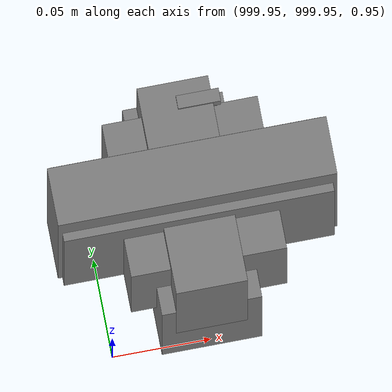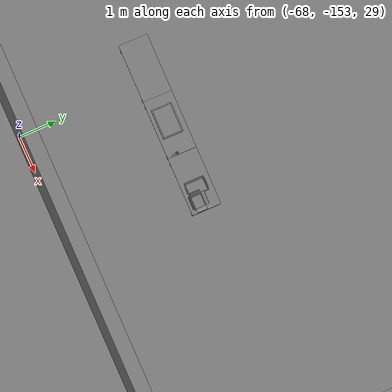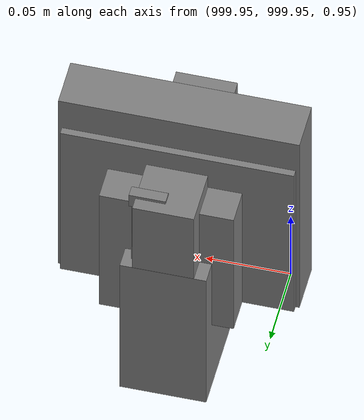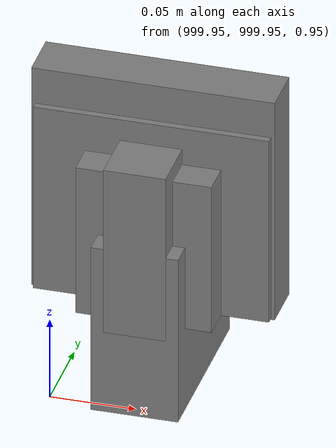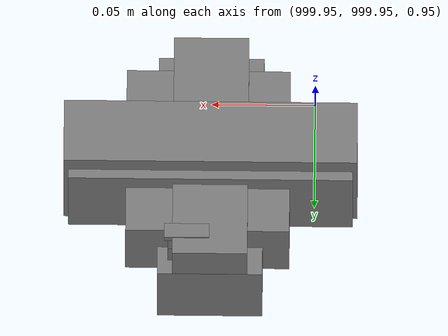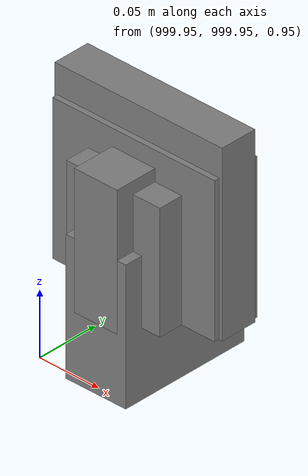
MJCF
<mujoco>
    <option gravity="0.000000000 0.000000000 -9.810000420" timestep="0.0049999999" integrator="implicitfast" density="1.225" viscosity="1.8000001e-05" noslip_iterations="10" iterations="100" sdf_iterations="50">
        <flag multiccd="disable"/>
    </option>
    <size memory="1000M"/>
    <compiler coordinate="local"/>
    <worldbody>
        <light cutoff="30" pos="0 1 1" dir="0 -1 -2"/>
        <light cutoff="30" pos="0 -1 1" dir="0 1 -2"/>
        <body pos="-64.866622925 -149.383972168 30.183746338" euler="89.999984741 89.999946594 0.000000000" name="openloong_gripper_2f85_fix_base_usda_bluebox_01">
            <geom contype="1" conaffinity="1" density="1000" type="box" material="" rgba="0.500000000 0.500000000 0.500000000 1.000000000" solimp="0.899999976 0.949999988 0.001000000" friction="1.000000000 0.005000000 0.000100000" solref="0.020000000 1.000000000" margin="0" condim="3" group="0" pos="0.276580811 0.187225342 0.000068665" quat="0.707106948 0.000077471 0.707106352 0.000077486" size="0.100000001 0.057999998 0.010000000" name="openloong_gripper_2f85_fix_base_usda_geom_AEBE7E5F_B178_49BF_B434_0B1868A05072"/>
            <geom contype="1" conaffinity="1" density="1000" type="box" material="" rgba="0.500000000 0.500000000 0.500000000 1.000000000" solimp="0.899999976 0.949999988 0.001000000" friction="1.000000000 0.005000000 0.000100000" solref="0.020000000 1.000000000" margin="0" condim="3" group="0" pos="0.000000000 0.002883911 0.000000000" quat="0.999999881 0.000000000 0.000000000 0.000000000" size="0.254000008 0.003000000 0.172000006" name="openloong_gripper_2f85_fix_base_usda_geom_11B61F4C_7479_4583_9DCE_A297A5584807"/>
            <geom contype="1" conaffinity="1" density="1000" type="box" material="" rgba="0.500000000 0.500000000 0.500000000 1.000000000" solimp="0.899999976 0.949999988 0.001000000" friction="1.000000000 0.005000000 0.000100000" solref="0.020000000 1.000000000" margin="0" condim="3" group="0" pos="0.000000000 0.124874115 0.173484802" quat="0.999796331 0.020176515 -0.000000015 0.000000030" size="0.259999990 0.119999997 0.007000000" name="openloong_gripper_2f85_fix_base_usda_geom_B727CC29_19CF_443B_B8A9_886EEA4D87D8"/>
            <geom contype="1" conaffinity="1" density="1000" type="box" material="" rgba="0.500000000 0.500000000 0.500000000 1.000000000" solimp="0.899999976 0.949999988 0.001000000" friction="1.000000000 0.005000000 0.000100000" solref="0.020000000 1.000000000" margin="0" condim="3" group="0" pos="0.000000000 0.124874115 -0.173469543" quat="0.999796331 -0.020176545 -0.000000015 0.000000000" size="0.259999990 0.119999997 0.007000000" name="openloong_gripper_2f85_fix_base_usda_geom_186CA2B8_A1C4_44F6_9EA8_A14299D169ED"/>
            <geom contype="1" conaffinity="1" density="1000" type="box" material="" rgba="0.500000000 0.500000000 0.500000000 1.000000000" solimp="0.899999976 0.949999988 0.001000000" friction="1.000000000 0.005000000 0.000100000" solref="0.020000000 1.000000000" margin="0" condim="3" group="0" pos="0.000000000 0.214008331 0.188980103" quat="0.999912977 0.013176724 0.000000015 0.000000000" size="0.259999990 0.029999999 0.012500000" name="openloong_gripper_2f85_fix_base_usda_geom_AE475642_C4CA_4873_8EE4_430A5D936CE5"/>
            <geom contype="1" conaffinity="1" density="1000" type="box" material="" rgba="0.500000000 0.500000000 0.500000000 1.000000000" solimp="0.899999976 0.949999988 0.001000000" friction="1.000000000 0.005000000 0.000100000" solref="0.020000000 1.000000000" margin="0" condim="3" group="0" pos="-0.258361816 0.125289917 0.001876831" quat="0.702796936 -0.020792112 0.710783124 0.020769298" size="0.189999998 0.119999997 0.009000000" name="openloong_gripper_2f85_fix_base_usda_geom_F85402B1_4490_42B6_BD56_B6FE6A0A0E1E"/>
            <geom contype="1" conaffinity="1" density="1000" type="box" material="" rgba="0.500000000 0.500000000 0.500000000 1.000000000" solimp="0.899999976 0.949999988 0.001000000" friction="1.000000000 0.005000000 0.000100000" solref="0.020000000 1.000000000" margin="0" condim="3" group="0" pos="0.000000000 0.214008331 -0.188980103" quat="0.999912977 -0.013176769 0.000000030 0.000000015" size="0.259999990 0.029999999 0.012500000" name="openloong_gripper_2f85_fix_base_usda_geom_356E126D_E379_493B_8067_23AFA4AC9028"/>
            <geom contype="1" conaffinity="1" density="1000" type="box" material="" rgba="0.500000000 0.500000000 0.500000000 1.000000000" solimp="0.899999976 0.949999988 0.001000000" friction="1.000000000 0.005000000 0.000100000" solref="0.020000000 1.000000000" margin="0" condim="3" group="0" pos="-0.276611328 0.187225342 0.000068665" quat="0.707106650 0.000077441 0.707106709 0.000077456" size="0.100000001 0.057999998 0.010000000" name="openloong_gripper_2f85_fix_base_usda_geom_933D3C59_9C21_4AC1_B9E3_BE7A4D13C124"/>
            <geom contype="1" conaffinity="1" density="1000" type="box" material="" rgba="0.500000000 0.500000000 0.500000000 1.000000000" solimp="0.899999976 0.949999988 0.001000000" friction="1.000000000 0.005000000 0.000100000" solref="0.020000000 1.000000000" margin="0" condim="3" group="0" pos="0.258331299 0.125289917 0.001876831" quat="0.702851415 0.018856421 0.710823774 -0.019329369" size="0.189999998 0.119999997 0.009000000" name="openloong_gripper_2f85_fix_base_usda_geom_1C0AF4EB_2A54_4E38_86C5_7D2BF9752BDD"/>
            <freejoint name="openloong_gripper_2f85_fix_base_usda_bluebox_01_joint"/>
            <site size="0.005000000 0.005000000 0.005000000" rgba="0.500000000 0.500000000 0.500000000 1.000000000" pos="0.000000000 0.000000000 0.000000000" quat="0.999961913 0.008726534 0.000000000 0.000000000" group="0" type="sphere" name="openloong_gripper_2f85_fix_base_usda_bluebox_01site"/>
        </body>
        <body pos="-64.496299744 -149.491867065 30.235729218" euler="0.000000000 0.000000000 89.999946594" name="openloong_gripper_2f85_fix_base_usda_cardboardbox_01">
            <geom contype="1" conaffinity="1" density="1000" type="box" material="" rgba="0.500000000 0.500000000 0.500000000 1.000000000" solimp="0.899999976 0.949999988 0.001000000" friction="1.000000000 0.005000000 0.000100000" solref="0.020000000 1.000000000" margin="0" condim="3" group="0" pos="-0.003166199 -0.004086494 0.005052090" quat="1.000000000 0.000000000 0.000000000 0.000000000" size="0.142499998 0.177500010 0.005000000" name="openloong_gripper_2f85_fix_base_usda_geom_6A042B92_D084_42F3_B72F_E2EA5383D932"/>
            <geom contype="1" conaffinity="1" density="1000" type="box" material="" rgba="0.500000000 0.500000000 0.500000000 1.000000000" solimp="0.899999976 0.949999988 0.001000000" friction="1.000000000 0.005000000 0.000100000" solref="0.020000000 1.000000000" margin="0" condim="3" group="0" pos="-0.003166199 0.170316696 0.150570869" quat="1.000000000 0.000000000 0.000000000 0.000000000" size="0.142499998 0.005000000 0.149999991" name="openloong_gripper_2f85_fix_base_usda_geom_DF0E1352_849C_4AD2_AAE9_5AB78944C134"/>
            <geom contype="1" conaffinity="1" density="1000" type="box" material="" rgba="0.500000000 0.500000000 0.500000000 1.000000000" solimp="0.899999976 0.949999988 0.001000000" friction="1.000000000 0.005000000 0.000100000" solref="0.020000000 1.000000000" margin="0" condim="3" group="0" pos="-0.147399902 -0.005307198 0.150570869" quat="1.000000000 0.000000000 0.000000000 0.000000000" size="0.005000000 0.177500010 0.149999991" name="openloong_gripper_2f85_fix_base_usda_geom_6C12B1B2_23D6_4757_BE4E_AB040E0A1F6E"/>
            <geom contype="1" conaffinity="1" density="1000" type="box" material="" rgba="0.500000000 0.500000000 0.500000000 1.000000000" solimp="0.899999976 0.949999988 0.001000000" friction="1.000000000 0.005000000 0.000100000" solref="0.020000000 1.000000000" margin="0" condim="3" group="0" pos="0.140275955 -0.005307198 0.150570869" quat="1.000000000 0.000000000 0.000000000 0.000000000" size="0.005000000 0.177500010 0.149999991" name="openloong_gripper_2f85_fix_base_usda_geom_4AE20962_0AC2_4907_ABA4_2AAB7561D481"/>
            <geom contype="1" conaffinity="1" density="1000" type="box" material="" rgba="0.500000000 0.500000000 0.500000000 1.000000000" solimp="0.899999976 0.949999988 0.001000000" friction="1.000000000 0.005000000 0.000100000" solref="0.020000000 1.000000000" margin="0" condim="3" group="0" pos="-0.003166199 -0.181550980 0.150570869" quat="1.000000000 0.000000000 0.000000000 0.000000000" size="0.142499998 0.005000000 0.149999991" name="openloong_gripper_2f85_fix_base_usda_geom_9B8CE984_32F3_47CB_A6A1_4E1096D3EC09"/>
            <freejoint name="openloong_gripper_2f85_fix_base_usda_cardboardbox_01_joint"/>
            <site size="0.005000000 0.005000000 0.005000000" rgba="0.500000000 0.500000000 0.500000000 1.000000000" pos="0.000000000 0.000000000 0.000000000" quat="0.999961913 0.008726535 0.000000000 0.000000000" group="0" type="sphere" name="openloong_gripper_2f85_fix_base_usda_site_1A71E088_0B18_4536_8BC0_0A826B5975ED"/>
            <body pos="0.139160156 -0.004048347 0.301930904" euler="-179.999954224 49.383502960 179.999954224" name="openloong_gripper_2f85_fix_base_usda_A1_006">
                <geom contype="1" conaffinity="1" density="1000" type="box" material="" rgba="0.500000000 0.500000000 0.500000000 1.000000000" solimp="0.899999976 0.949999988 0.001000000" friction="1.000000000 0.005000000 0.000100000" solref="0.020000000 1.000000000" margin="0" condim="3" group="0" pos="-0.071587563 0.000009537 0.001745224" quat="0.999999881 0.000000000 0.000000000 0.000000000" size="0.071249999 0.179999992 0.002500000" name="openloong_gripper_2f85_fix_base_usda_geom_04074DC8_2A5E_41EC_8B7F_15B2484C5703"/>
                <joint armature="0" stiffness="0.07" damping="0.0099999998" axis="0.000000 1.000000 0.000000" type="hinge" name="openloong_gripper_2f85_fix_base_usda_A1_006"/>
            </body>
            <body pos="-0.145902634 -0.004086494 0.301938057" euler="-180.000000000 -60.000011444 -180.000000000" name="openloong_gripper_2f85_fix_base_usda_A2_006">
                <geom contype="1" conaffinity="1" density="1000" type="box" material="" rgba="0.500000000 0.500000000 0.500000000 1.000000000" solimp="0.899999976 0.949999988 0.001000000" friction="1.000000000 0.005000000 0.000100000" solref="0.020000000 1.000000000" margin="0" condim="3" group="0" pos="0.071268082 0.000009537 0.002717972" quat="0.000002921 0.000000000 -0.000000030 0.999999881" size="0.071249999 0.179999992 0.002500000" name="openloong_gripper_2f85_fix_base_usda_geom_06B1AB64_39F7_4B59_B046_A22EA3198960"/>
                <joint armature="0" stiffness="0.07" damping="0.0099999998" axis="0.000000 1.000000 0.000000" type="hinge" name="openloong_gripper_2f85_fix_base_usda_A2_006"/>
            </body>
            <body pos="-0.003385544 0.175991058 0.301930904" euler="-125.858116150 -0.000004561 0.000002331" name="openloong_gripper_2f85_fix_base_usda_B2_006">
                <geom contype="1" conaffinity="1" density="1000" type="box" material="" rgba="0.500000000 0.500000000 0.500000000 1.000000000" solimp="0.899999976 0.949999988 0.001000000" friction="1.000000000 0.005000000 0.000100000" solref="0.020000000 1.000000000" margin="0" condim="3" group="0" pos="0.000009537 -0.070939064 -0.002470016" quat="0.999614120 0.027776197 -0.000000015 0.000000030" size="0.137500003 0.064999998 0.005000000" name="openloong_gripper_2f85_fix_base_usda_geom_D1C992A6_A422_48AA_BBF5_3456670565D4"/>
                <joint armature="0" stiffness="0.07" damping="0.0099999998" axis="1.000000 0.000000 0.000000" type="hinge" name="openloong_gripper_2f85_fix_base_usda_B2_006"/>
            </body>
            <body pos="-0.003385544 -0.184140205 0.301938057" euler="147.805557251 0.000000000 0.000000000" name="openloong_gripper_2f85_fix_base_usda_B1_006">
                <geom contype="1" conaffinity="1" density="1000" type="box" material="" rgba="0.500000000 0.500000000 0.500000000 1.000000000" solimp="0.899999976 0.949999988 0.001000000" friction="1.000000000 0.005000000 0.000100000" solref="0.020000000 1.000000000" margin="0" condim="3" group="0" pos="-0.000028610 0.070202351 -0.002703667" quat="0.999614179 -0.027776167 0.000000000 0.000000000" size="0.137500003 0.064999998 0.005000000" name="openloong_gripper_2f85_fix_base_usda_geom_EE505FCE_929E_472B_ADE2_F061E26CAEE3"/>
                <joint armature="0" stiffness="0.07" damping="0.0099999998" axis="1.000000 0.000000 0.000000" type="hinge" name="openloong_gripper_2f85_fix_base_usda_B1_006"/>
            </body>
        </body>
        <body pos="-65.882858276 -149.481979370 30.229999542" euler="-64.487716675 0.000000000 0.000000000" name="openloong_gripper_2f85_fix_base_usda_Barcode">
            <geom contype="1" conaffinity="1" density="1000" type="box" material="" rgba="0.500000000 0.500000000 0.500000000 1.000000000" solimp="0.899999976 0.949999988 0.001000000" friction="1.000000000 0.005000000 0.000100000" solref="0.020000000 1.000000000" margin="0" condim="3" group="0" pos="0.000000000 0.013038635 0.001419067" quat="0.000000000 0.000000000 0.000000000 1.000000119" size="0.034000002 0.010000000 0.017999999" name="openloong_gripper_2f85_fix_base_usda_geom_9FDFD013_7ADE_4589_9476_BACD5F3F9722"/>
            <geom contype="1" conaffinity="1" density="1000" type="box" material="" rgba="0.500000000 0.500000000 0.500000000 1.000000000" solimp="0.899999976 0.949999988 0.001000000" friction="1.000000000 0.005000000 0.000100000" solref="0.020000000 1.000000000" margin="0" condim="3" group="0" pos="0.000000000 -0.035301208 -0.007095337" quat="0.000000000 0.000000000 -0.043619365 0.999048233" size="0.028999999 0.010000000 0.020000000" name="openloong_gripper_2f85_fix_base_usda_geom_77E21B62_D3BB_4803_AFF0_1EDF7855BD53"/>
            <geom contype="1" conaffinity="1" density="1000" type="box" material="" rgba="0.500000000 0.500000000 0.500000000 1.000000000" solimp="0.899999976 0.949999988 0.001000000" friction="1.000000000 0.005000000 0.000100000" solref="0.020000000 1.000000000" margin="0" condim="3" group="0" pos="0.000000000 -0.043411255 -0.011749268" quat="0.922262907 0.386563420 0.000000000 0.000000000" size="0.026000001 0.010000000 0.020000000" name="openloong_gripper_2f85_fix_base_usda_geom_5D6CDB2B_1AD1_49FA_8796_B5F5A6E7B228"/>
            <geom contype="1" conaffinity="1" density="1000" type="box" material="" rgba="0.500000000 0.500000000 0.500000000 1.000000000" solimp="0.899999976 0.949999988 0.001000000" friction="1.000000000 0.005000000 0.000100000" solref="0.020000000 1.000000000" margin="0" condim="3" group="0" pos="0.000000000 -0.016967773 -0.031860352" quat="0.000000000 0.000000000 0.000000000 1.000000119" size="0.008000000 0.010000000 0.013000000" name="openloong_gripper_2f85_fix_base_usda_geom_A532E068_4A0D_4B2A_8370_3D513BB902E2"/>
            <geom contype="1" conaffinity="1" density="1000" type="box" material="" rgba="0.500000000 0.500000000 0.500000000 1.000000000" solimp="0.899999976 0.949999988 0.001000000" friction="1.000000000 0.005000000 0.000100000" solref="0.020000000 1.000000000" margin="0" condim="3" group="0" pos="0.000000000 -0.001869202 0.000312805" quat="0.953716993 0.300705761 0.000000000 0.000000000" size="0.032000002 0.010000000 0.018999999" name="openloong_gripper_2f85_fix_base_usda_geom_5128C59D_86EA_4FDE_AA54_0BB419C559FE"/>
            <geom contype="1" conaffinity="1" density="1000" type="box" material="" rgba="0.500000000 0.500000000 0.500000000 1.000000000" solimp="0.899999976 0.949999988 0.001000000" friction="1.000000000 0.005000000 0.000100000" solref="0.020000000 1.000000000" margin="0" condim="3" group="0" pos="0.000000000 -0.019531250 -0.003173828" quat="0.953716993 0.300705761 0.000000000 0.000000000" size="0.030999999 0.010000000 0.020000000" name="openloong_gripper_2f85_fix_base_usda_geom_2131D21B_B819_48DE_A741_C52F62904E8D"/>
            <geom contype="1" conaffinity="1" density="1000" type="box" material="" rgba="0.500000000 0.500000000 0.500000000 1.000000000" solimp="0.899999976 0.949999988 0.001000000" friction="1.000000000 0.005000000 0.000100000" solref="0.020000000 1.000000000" margin="0" condim="3" group="0" pos="0.000000000 -0.035301208 -0.007095337" quat="0.953716993 0.300705761 0.000000000 0.000000000" size="0.028999999 0.010000000 0.020000000" name="openloong_gripper_2f85_fix_base_usda_geom_77016FA4_070F_4A84_8658_C7E3441D2315"/>
            <geom contype="1" conaffinity="1" density="1000" type="box" material="" rgba="0.500000000 0.500000000 0.500000000 1.000000000" solimp="0.899999976 0.949999988 0.001000000" friction="1.000000000 0.005000000 0.000100000" solref="0.020000000 1.000000000" margin="0" condim="3" group="0" pos="0.000000000 -0.042617798 -0.071121216" quat="0.000000000 0.000000000 0.000000000 1.000000119" size="0.013000000 0.021000000 0.059999999" name="openloong_gripper_2f85_fix_base_usda_geom_AECA9213_7898_4DA9_93D8_42B5242C20EE"/>
            <freejoint name="openloong_gripper_2f85_fix_base_usda_Barcode_joint"/>
            <site size="0.005000000 0.005000000 0.005000000" rgba="0.500000000 0.500000000 0.500000000 1.000000000" pos="0.000000000 0.000000000 0.000000000" quat="1.000000000 0.000000000 0.000000000 0.000000000" group="0" type="sphere" name="openloong_gripper_2f85_fix_base_usda_Barcode_site"/>
        </body>
        <body pos="-66.745018005 -149.392349243 30.184000015" euler="0.000000000 0.000000000 89.999946594" name="[22332270200063]_Basket_01">
            <geom contype="1" conaffinity="1" density="1000" type="box" material="" rgba="0.500000000 0.500000000 0.500000000 1.000000000" solimp="0.899999976 0.949999988 0.001000000" friction="1.000000000 0.005000000 0.000100000" solref="0.020000000 1.000000000" margin="0" condim="3" group="0" pos="-0.052425385 0.389207840 0.089787483" quat="0.707107008 0.000000000 0.000000000 0.707106411" size="0.014249999 0.014249999 0.059999999" name="[22332270200063]_geom_D8C67622_0403_4367_980B_08FD50F90654"/>
            <geom contype="1" conaffinity="1" density="1000" type="box" material="" rgba="0.500000000 0.500000000 0.500000000 1.000000000" solimp="0.899999976 0.949999988 0.001000000" friction="1.000000000 0.005000000 0.000100000" solref="0.020000000 1.000000000" margin="0" condim="3" group="0" pos="0.264015198 -0.133043289 0.089787483" quat="0.707107008 0.000000000 0.000000000 0.707106411" size="0.014249999 0.014249999 0.059999999" name="[22332270200063]_geom_0FD216B4_0DA2_4576_8FDD_A0A40D995108"/>
            <geom contype="1" conaffinity="1" density="1000" type="box" material="" rgba="0.500000000 0.500000000 0.500000000 1.000000000" solimp="0.899999976 0.949999988 0.001000000" friction="1.000000000 0.005000000 0.000100000" solref="0.020000000 1.000000000" margin="0" condim="3" group="0" pos="-0.264015198 -0.265548706 0.089793205" quat="0.707107008 0.000000000 0.000000000 0.707106411" size="0.014249999 0.014249999 0.059999999" name="[22332270200063]_geom_04D2A601_F3DA_450E_9843_5AEB198427DF"/>
            <geom contype="1" conaffinity="1" density="1000" type="box" material="" rgba="0.500000000 0.500000000 0.500000000 1.000000000" solimp="0.899999976 0.949999988 0.001000000" friction="1.000000000 0.005000000 0.000100000" solref="0.020000000 1.000000000" margin="0" condim="3" group="0" pos="-0.160263062 -0.389322281 0.089793205" quat="0.707107008 0.000000000 0.000000000 0.707106411" size="0.014249999 0.014249999 0.059999999" name="[22332270200063]_geom_3B1FD124_F864_4FAB_AE83_89AA6A5B7A4F"/>
            <geom contype="1" conaffinity="1" density="1000" type="box" material="" rgba="0.500000000 0.500000000 0.500000000 1.000000000" solimp="0.899999976 0.949999988 0.001000000" friction="1.000000000 0.005000000 0.000100000" solref="0.020000000 1.000000000" margin="0" condim="3" group="0" pos="0.162265778 -0.389322281 0.089787483" quat="0.707107008 0.000000000 0.000000000 0.707106411" size="0.014249999 0.014249999 0.059999999" name="[22332270200063]_geom_B1963696_3915_4906_AA20_A2EB195A9C77"/>
            <geom contype="1" conaffinity="1" density="1000" type="box" material="" rgba="0.500000000 0.500000000 0.500000000 1.000000000" solimp="0.899999976 0.949999988 0.001000000" friction="1.000000000 0.005000000 0.000100000" solref="0.020000000 1.000000000" margin="0" condim="3" group="0" pos="0.264015198 0.389207840 0.089787483" quat="0.707107008 0.000000000 0.000000000 0.707106411" size="0.014249999 0.014249999 0.059999999" name="[22332270200063]_geom_579C5107_F3BF_4022_9CDB_276A215DFD49"/>
            <geom contype="1" conaffinity="1" density="1000" type="box" material="" rgba="0.500000000 0.500000000 0.500000000 1.000000000" solimp="0.899999976 0.949999988 0.001000000" friction="1.000000000 0.005000000 0.000100000" solref="0.020000000 1.000000000" margin="0" condim="3" group="0" pos="-0.264015198 -0.133043289 0.089793205" quat="0.707107008 0.000000000 0.000000000 0.707106411" size="0.014249999 0.014249999 0.059999999" name="[22332270200063]_geom_A8800F97_4C3B_4E18_B4E8_A649DEA90AD9"/>
            <geom contype="1" conaffinity="1" density="1000" type="box" material="" rgba="0.500000000 0.500000000 0.500000000 1.000000000" solimp="0.899999976 0.949999988 0.001000000" friction="1.000000000 0.005000000 0.000100000" solref="0.020000000 1.000000000" margin="0" condim="3" group="0" pos="-0.264026642 0.269256592 0.089793205" quat="0.707107008 0.000000000 0.000000000 0.707106411" size="0.014249999 0.014249999 0.059999999" name="[22332270200063]_geom_524B9C83_2E22_4949_8BC8_93C4F94C40AE"/>
            <geom contype="1" conaffinity="1" density="1000" type="box" material="" rgba="0.500000000 0.500000000 0.500000000 1.000000000" solimp="0.899999976 0.949999988 0.001000000" friction="1.000000000 0.005000000 0.000100000" solref="0.020000000 1.000000000" margin="0" condim="3" group="0" pos="0.054462433 0.389207840 0.089787483" quat="0.707107008 0.000000000 0.000000000 0.707106411" size="0.014249999 0.014249999 0.059999999" name="[22332270200063]_geom_EEC23EE6_7D68_4258_853A_4DE135C5124E"/>
            <geom contype="1" conaffinity="1" density="1000" type="box" material="" rgba="0.500000000 0.500000000 0.500000000 1.000000000" solimp="0.899999976 0.949999988 0.001000000" friction="1.000000000 0.005000000 0.000100000" solref="0.020000000 1.000000000" margin="0" condim="3" group="0" pos="0.054462433 -0.389322281 0.089787483" quat="0.707107008 0.000000000 0.000000000 0.707106411" size="0.014249999 0.014249999 0.059999999" name="[22332270200063]_geom_14B6C6AD_99DB_4842_B01F_8ECCEBED2A6C"/>
            <geom contype="1" conaffinity="1" density="1000" type="box" material="" rgba="0.500000000 0.500000000 0.500000000 1.000000000" solimp="0.899999976 0.949999988 0.001000000" friction="1.000000000 0.005000000 0.000100000" solref="0.020000000 1.000000000" margin="0" condim="3" group="0" pos="0.264015198 0.269256592 0.089793205" quat="0.707107008 0.000000000 0.000000000 0.707106411" size="0.014249999 0.014249999 0.059999999" name="[22332270200063]_geom_30581F3D_D20D_45F0_B5B8_18305DA2B916"/>
            <geom contype="1" conaffinity="1" density="1000" type="box" material="" rgba="0.500000000 0.500000000 0.500000000 1.000000000" solimp="0.899999976 0.949999988 0.001000000" friction="1.000000000 0.005000000 0.000100000" solref="0.020000000 1.000000000" margin="0" condim="3" group="0" pos="0.264015198 -0.389322281 0.089787483" quat="0.707107008 0.000000000 0.000000000 0.707106411" size="0.014249999 0.014249999 0.059999999" name="[22332270200063]_geom_00037AD3_A0D1_4584_BA9C_042C6DA5AD84"/>
            <geom contype="1" conaffinity="1" density="1000" type="box" material="" rgba="0.500000000 0.500000000 0.500000000 1.000000000" solimp="0.899999976 0.949999988 0.001000000" friction="1.000000000 0.005000000 0.000100000" solref="0.020000000 1.000000000" margin="0" condim="3" group="0" pos="0.000000000 0.000000000 0.015998840" quat="0.707107008 0.000000000 0.000000000 0.707106411" size="0.403499991 0.279000014 0.015750000" name="[22332270200063]_geom_EF4B7412_F37C_491C_A46E_1781F2380708"/>
            <geom contype="1" conaffinity="1" density="1000" type="box" material="" rgba="0.500000000 0.500000000 0.500000000 1.000000000" solimp="0.899999976 0.949999988 0.001000000" friction="1.000000000 0.005000000 0.000100000" solref="0.020000000 1.000000000" margin="0" condim="3" group="0" pos="0.000000000 -0.389476776 0.163619041" quat="0.707107008 0.000000000 0.000000000 0.707106411" size="0.015000000 0.277500004 0.015750000" name="[22332270200063]_geom_01CEBCA6_FEF1_4318_968B_A745419B5C52"/>
            <geom contype="1" conaffinity="1" density="1000" type="box" material="" rgba="0.500000000 0.500000000 0.500000000 1.000000000" solimp="0.899999976 0.949999988 0.001000000" friction="1.000000000 0.005000000 0.000100000" solref="0.020000000 1.000000000" margin="0" condim="3" group="0" pos="0.162265778 0.389207840 0.089787483" quat="0.707107008 0.000000000 0.000000000 0.707106411" size="0.014249999 0.014249999 0.059999999" name="[22332270200063]_geom_88C59983_F8D8_4D55_873E_DFD6DCB34FD2"/>
            <geom contype="1" conaffinity="1" density="1000" type="box" material="" rgba="0.500000000 0.500000000 0.500000000 1.000000000" solimp="0.899999976 0.949999988 0.001000000" friction="1.000000000 0.005000000 0.000100000" solref="0.020000000 1.000000000" margin="0" condim="3" group="0" pos="0.000000000 0.389471054 0.163619041" quat="0.707107008 0.000000000 0.000000000 0.707106411" size="0.015000000 0.277500004 0.015750000" name="[22332270200063]_geom_3CEE628C_29AC_4AB6_9678_A746C0546FB3"/>
            <geom contype="1" conaffinity="1" density="1000" type="box" material="" rgba="0.500000000 0.500000000 0.500000000 1.000000000" solimp="0.899999976 0.949999988 0.001000000" friction="1.000000000 0.005000000 0.000100000" solref="0.020000000 1.000000000" margin="0" condim="3" group="0" pos="-0.263511658 0.000000000 0.163619041" quat="0.707107008 0.000000000 0.000000000 0.707106411" size="0.403499991 0.015000000 0.015750000" name="[22332270200063]_geom_91C5EBB3_456D_423A_95AF_D75D49CCB070"/>
            <geom contype="1" conaffinity="1" density="1000" type="box" material="" rgba="0.500000000 0.500000000 0.500000000 1.000000000" solimp="0.899999976 0.949999988 0.001000000" friction="1.000000000 0.005000000 0.000100000" solref="0.020000000 1.000000000" margin="0" condim="3" group="0" pos="-0.264015198 0.141334534 0.089793205" quat="0.707107008 0.000000000 0.000000000 0.707106411" size="0.014249999 0.014249999 0.059999999" name="[22332270200063]_geom_4B0AB442_AC87_42EC_B140_55493B618BFE"/>
            <geom contype="1" conaffinity="1" density="1000" type="box" material="" rgba="0.500000000 0.500000000 0.500000000 1.000000000" solimp="0.899999976 0.949999988 0.001000000" friction="1.000000000 0.005000000 0.000100000" solref="0.020000000 1.000000000" margin="0" condim="3" group="0" pos="0.264015198 -0.265548706 0.089787483" quat="0.707107008 0.000000000 0.000000000 0.707106411" size="0.014249999 0.014249999 0.059999999" name="[22332270200063]_geom_1B63C3AC_87BC_4044_860C_3559CAC05C3E"/>
            <geom contype="1" conaffinity="1" density="1000" type="box" material="" rgba="0.500000000 0.500000000 0.500000000 1.000000000" solimp="0.899999976 0.949999988 0.001000000" friction="1.000000000 0.005000000 0.000100000" solref="0.020000000 1.000000000" margin="0" condim="3" group="0" pos="-0.160263062 0.389207840 0.089787483" quat="0.707107008 0.000000000 0.000000000 0.707106411" size="0.014249999 0.014249999 0.059999999" name="[22332270200063]_geom_E9509C9D_378F_4D14_BE3B_18646F762FFA"/>
            <geom contype="1" conaffinity="1" density="1000" type="box" material="" rgba="0.500000000 0.500000000 0.500000000 1.000000000" solimp="0.899999976 0.949999988 0.001000000" friction="1.000000000 0.005000000 0.000100000" solref="0.020000000 1.000000000" margin="0" condim="3" group="0" pos="-0.052425385 -0.389322281 0.089787483" quat="0.707107008 0.000000000 0.000000000 0.707106411" size="0.014249999 0.014249999 0.059999999" name="[22332270200063]_geom_9B484662_5712_402B_A259_C6D833514958"/>
            <geom contype="1" conaffinity="1" density="1000" type="box" material="" rgba="0.500000000 0.500000000 0.500000000 1.000000000" solimp="0.899999976 0.949999988 0.001000000" friction="1.000000000 0.005000000 0.000100000" solref="0.020000000 1.000000000" margin="0" condim="3" group="0" pos="-0.264026642 -0.389322281 0.089793205" quat="0.707107008 0.000000000 0.000000000 0.707106411" size="0.014249999 0.014249999 0.059999999" name="[22332270200063]_geom_C5AC40A5_F5D0_40AA_898B_17E2E69CFF76"/>
            <geom contype="1" conaffinity="1" density="1000" type="box" material="" rgba="0.500000000 0.500000000 0.500000000 1.000000000" solimp="0.899999976 0.949999988 0.001000000" friction="1.000000000 0.005000000 0.000100000" solref="0.020000000 1.000000000" margin="0" condim="3" group="0" pos="0.264015198 0.141334534 0.089787483" quat="0.707107008 0.000000000 0.000000000 0.707106411" size="0.014249999 0.014249999 0.059999999" name="[22332270200063]_geom_2FE108BC_5C5B_46D4_867F_B4F5214815DD"/>
            <geom contype="1" conaffinity="1" density="1000" type="box" material="" rgba="0.500000000 0.500000000 0.500000000 1.000000000" solimp="0.899999976 0.949999988 0.001000000" friction="1.000000000 0.005000000 0.000100000" solref="0.020000000 1.000000000" margin="0" condim="3" group="0" pos="-0.264015198 0.389207840 0.089793205" quat="0.707107008 0.000000000 0.000000000 0.707106411" size="0.014249999 0.014249999 0.059999999" name="[22332270200063]_geom_D3B615A4_1223_4495_95D2_C76B61105E56"/>
            <geom contype="1" conaffinity="1" density="1000" type="box" material="" rgba="0.500000000 0.500000000 0.500000000 1.000000000" solimp="0.899999976 0.949999988 0.001000000" friction="1.000000000 0.005000000 0.000100000" solref="0.020000000 1.000000000" margin="0" condim="3" group="0" pos="0.264015198 0.004480362 0.089787483" quat="0.707107008 0.000000000 0.000000000 0.707106411" size="0.014249999 0.014249999 0.059999999" name="[22332270200063]_geom_422FD005_9A03_4D2B_AA11_E27F983FFD94"/>
            <geom contype="1" conaffinity="1" density="1000" type="box" material="" rgba="0.500000000 0.500000000 0.500000000 1.000000000" solimp="0.899999976 0.949999988 0.001000000" friction="1.000000000 0.005000000 0.000100000" solref="0.020000000 1.000000000" margin="0" condim="3" group="0" pos="0.263694763 -0.000011444 0.163619041" quat="0.707107008 0.000000000 0.000000000 0.707106411" size="0.403499991 0.015000000 0.015750000" name="[22332270200063]_geom_80E5D75C_564C_4393_8D7F_E08C41DDFE8A"/>
            <geom contype="1" conaffinity="1" density="1000" type="box" material="" rgba="0.500000000 0.500000000 0.500000000 1.000000000" solimp="0.899999976 0.949999988 0.001000000" friction="1.000000000 0.005000000 0.000100000" solref="0.020000000 1.000000000" margin="0" condim="3" group="0" pos="-0.264015198 0.004480362 0.089793205" quat="0.707107008 0.000000000 0.000000000 0.707106411" size="0.014249999 0.014249999 0.059999999" name="[22332270200063]_geom_FF66F68A_DDB2_48F4_84D1_87A8D91049DA"/>
            <freejoint name="[22332270200063]_joint_FC920EAB_DF62_4734_836A_D44D2059EF42"/>
        </body>
        <body pos="0.000000000 0.000000000 0.000000000" euler="0.000000000 0.000000000 0.000000000" name="Static Objects_Static Objects">
            <geom contype="1" conaffinity="1" density="1000" type="box" material="" rgba="0.500000000 0.500000000 0.500000000 1.000000000" solimp="0.899999976 0.949999988 0.001000000" friction="1.000000000 0.005000000 0.000100000" solref="0.020000000 1.000000000" margin="0" condim="3" group="0" pos="-67.544113159 -149.365814209 29.727830887" quat="0.500000417 0.499999970 0.499999553 0.499999970" size="0.381000012 0.319999993 0.041000001" name="Static Objects_geom_40804F9B_0E62_4185_8414_46D7DC7103FE"/>
            <geom contype="1" conaffinity="1" density="1000" type="box" material="" rgba="0.500000000 0.500000000 0.500000000 1.000000000" solimp="0.899999976 0.949999988 0.001000000" friction="1.000000000 0.005000000 0.000100000" solref="0.020000000 1.000000000" margin="0" condim="3" group="0" pos="-68.239501953 -149.365814209 30.086868286" quat="0.500000417 0.499999970 0.499999553 0.499999970" size="0.370999992 0.039500002 0.745000005" name="Static Objects_geom_18F7A66A_C2D6_4139_9755_BEBD04756C44"/>
            <geom contype="1" conaffinity="1" density="1000" type="box" material="" rgba="0.500000000 0.500000000 0.500000000 1.000000000" solimp="0.899999976 0.949999988 0.001000000" friction="1.000000000 0.005000000 0.000100000" solref="0.020000000 1.000000000" margin="0" condim="3" group="0" pos="-68.239501953 -149.365814209 30.147235870" quat="0.500000417 0.499999970 0.499999553 0.499999970" size="0.400000006 0.022000000 0.800000012" name="Static Objects_geom_18A62CB4_2AEF_4DB7_828D_2DC8F1746077"/>
            <geom contype="1" conaffinity="1" density="1000" type="box" material="" rgba="0.500000000 0.500000000 0.500000000 1.000000000" solimp="0.899999976 0.949999988 0.001000000" friction="1.000000000 0.005000000 0.000100000" solref="0.020000000 1.000000000" margin="0" condim="3" group="0" pos="-68.934890747 -149.365814209 29.727830887" quat="0.500000417 0.499999970 0.499999553 0.499999970" size="0.381000012 0.319999993 0.041000001" name="Static Objects_geom_6DC6B9FE_E8AB_44AE_9F12_CBD6FEFB95FC"/>
            <geom contype="1" conaffinity="1" density="1000" type="box" material="" rgba="0.500000000 0.500000000 0.500000000 1.000000000" solimp="0.899999976 0.949999988 0.001000000" friction="1.000000000 0.005000000 0.000100000" solref="0.020000000 1.000000000" margin="0" condim="3" group="0" pos="-68.239501953 -149.365814209 29.561563492" quat="0.500000417 0.499999970 0.499999553 0.499999970" size="0.020000000 0.022000000 0.660000026" name="Static Objects_geom_16B6EB55_6691_478B_841C_2C55E38B931A"/>
            <geom contype="1" conaffinity="1" density="1000" type="box" material="" rgba="0.500000000 0.500000000 0.500000000 1.000000000" solimp="0.899999976 0.949999988 0.001000000" friction="1.000000000 0.005000000 0.000100000" solref="0.020000000 1.000000000" margin="0" condim="3" group="0" pos="-65.945671082 -149.365814209 29.727830887" quat="0.500000417 0.499999970 0.499999553 0.499999970" size="0.381000012 0.319999993 0.041000001" name="Static Objects_geom_5F4D8949_2A80_4C81_B5F2_EF35210F55B0"/>
            <geom contype="1" conaffinity="1" density="1000" type="box" material="" rgba="0.500000000 0.500000000 0.500000000 1.000000000" solimp="0.899999976 0.949999988 0.001000000" friction="1.000000000 0.005000000 0.000100000" solref="0.020000000 1.000000000" margin="0" condim="3" group="0" pos="-66.641059875 -149.365814209 30.086868286" quat="0.500000417 0.499999970 0.499999553 0.499999970" size="0.370999992 0.039500002 0.745000005" name="Static Objects_geom_C7C7CC1D_401F_4DF9_8C0B_D8DC85F01F57"/>
            <geom contype="1" conaffinity="1" density="1000" type="box" material="" rgba="0.500000000 0.500000000 0.500000000 1.000000000" solimp="0.899999976 0.949999988 0.001000000" friction="1.000000000 0.005000000 0.000100000" solref="0.020000000 1.000000000" margin="0" condim="3" group="0" pos="-66.641059875 -149.365814209 30.147235870" quat="0.500000417 0.499999970 0.499999553 0.499999970" size="0.400000006 0.022000000 0.800000012" name="Static Objects_geom_71AEA4E2_2F8D_462C_9435_740DE4556B5E"/>
            <geom contype="1" conaffinity="1" density="1000" type="box" material="" rgba="0.500000000 0.500000000 0.500000000 1.000000000" solimp="0.899999976 0.949999988 0.001000000" friction="1.000000000 0.005000000 0.000100000" solref="0.020000000 1.000000000" margin="0" condim="3" group="0" pos="-67.336448669 -149.365814209 29.727830887" quat="0.500000417 0.499999970 0.499999553 0.499999970" size="0.381000012 0.319999993 0.041000001" name="Static Objects_geom_42BEE3A8_DAB1_4EE1_9D88_22BB617BC0A5"/>
            <geom contype="1" conaffinity="1" density="1000" type="box" material="" rgba="0.500000000 0.500000000 0.500000000 1.000000000" solimp="0.899999976 0.949999988 0.001000000" friction="1.000000000 0.005000000 0.000100000" solref="0.020000000 1.000000000" margin="0" condim="3" group="0" pos="-66.641059875 -149.365814209 29.561563492" quat="0.500000417 0.499999970 0.499999553 0.499999970" size="0.020000000 0.022000000 0.660000026" name="Static Objects_geom_24D6B79C_8F3D_4259_9DE5_514D34D9A0B7"/>
            <geom contype="1" conaffinity="1" density="1000" type="box" material="" rgba="0.500000000 0.500000000 0.500000000 1.000000000" solimp="0.899999976 0.949999988 0.001000000" friction="1.000000000 0.005000000 0.000100000" solref="0.020000000 1.000000000" margin="0" condim="3" group="0" pos="-64.338577271 -149.365814209 29.727830887" quat="0.500000417 0.499999970 0.499999553 0.499999970" size="0.381000012 0.319999993 0.041000001" name="Static Objects_geom_CD8690A1_7071_4798_8182_9C787B35EA89"/>
            <geom contype="1" conaffinity="1" density="1000" type="box" material="" rgba="0.500000000 0.500000000 0.500000000 1.000000000" solimp="0.899999976 0.949999988 0.001000000" friction="1.000000000 0.005000000 0.000100000" solref="0.020000000 1.000000000" margin="0" condim="3" group="0" pos="-65.033966064 -149.365814209 30.086868286" quat="0.500000417 0.499999970 0.499999553 0.499999970" size="0.370999992 0.039500002 0.745000005" name="Static Objects_geom_B3D6C27E_0C7E_473F_BB1D_E04070C43E2D"/>
            <geom contype="1" conaffinity="1" density="1000" type="box" material="" rgba="0.500000000 0.500000000 0.500000000 1.000000000" solimp="0.899999976 0.949999988 0.001000000" friction="1.000000000 0.005000000 0.000100000" solref="0.020000000 1.000000000" margin="0" condim="3" group="0" pos="-65.033966064 -149.365814209 30.147235870" quat="0.500000417 0.499999970 0.499999553 0.499999970" size="0.400000006 0.022000000 0.800000012" name="Static Objects_geom_5E40C372_8BCD_4E60_9EF3_DB26770EBCBB"/>
            <geom contype="1" conaffinity="1" density="1000" type="box" material="" rgba="0.500000000 0.500000000 0.500000000 1.000000000" solimp="0.899999976 0.949999988 0.001000000" friction="1.000000000 0.005000000 0.000100000" solref="0.020000000 1.000000000" margin="0" condim="3" group="0" pos="-65.729354858 -149.365814209 29.727830887" quat="0.500000417 0.499999970 0.499999553 0.499999970" size="0.381000012 0.319999993 0.041000001" name="Static Objects_geom_DB6E145A_11EE_4F97_AEDF_DB585A888D77"/>
            <geom contype="1" conaffinity="1" density="1000" type="box" material="" rgba="0.500000000 0.500000000 0.500000000 1.000000000" solimp="0.899999976 0.949999988 0.001000000" friction="1.000000000 0.005000000 0.000100000" solref="0.020000000 1.000000000" margin="0" condim="3" group="0" pos="-65.033966064 -149.365814209 29.561563492" quat="0.500000417 0.499999970 0.499999553 0.499999970" size="0.020000000 0.022000000 0.660000026" name="Static Objects_geom_D5E29145_B21E_4025_910A_F81B4367278B"/>
            <geom contype="1" conaffinity="1" density="1000" type="box" material="" rgba="0.500000000 0.500000000 0.500000000 1.000000000" solimp="0.899999976 0.949999988 0.001000000" friction="1.000000000 0.005000000 0.000100000" solref="0.020000000 1.000000000" margin="0" condim="3" group="0" pos="-61.754566193 -137.853729248 33.906845093" quat="0.707107067 0.000000000 0.000000000 0.707106471" size="0.759999990 0.759999990 4.500000000" name="Static Objects_geom_1F109FF0_AE23_45DF_8E8E_4D7C611D0D80"/>
            <geom contype="1" conaffinity="1" density="1000" type="box" material="" rgba="0.500000000 0.500000000 0.500000000 1.000000000" solimp="0.899999976 0.949999988 0.001000000" friction="1.000000000 0.005000000 0.000100000" solref="0.020000000 1.000000000" margin="0" condim="3" group="0" pos="-57.511135101 -144.927108765 31.707921982" quat="1.000000000 0.000000000 0.000000000 0.000000000" size="0.200000003 8.000000000 2.299999952" name="Static Objects_geom_02DD2B4D_73F9_4D05_987E_D3B90C5C650B"/>
            <geom contype="1" conaffinity="1" density="1000" type="box" material="" rgba="0.500000000 0.500000000 0.500000000 1.000000000" solimp="0.899999976 0.949999988 0.001000000" friction="1.000000000 0.005000000 0.000100000" solref="0.020000000 1.000000000" margin="0" condim="3" group="0" pos="-80.517646790 -157.574050903 31.688196182" quat="0.707107067 0.000000000 0.000000000 0.707106471" size="0.600000024 0.600000024 2.299999952" name="Static Objects_geom_295E1023_35BD_47C6_9638_8D8248D320B2"/>
            <geom contype="1" conaffinity="1" density="1000" type="box" material="" rgba="0.500000000 0.500000000 0.500000000 1.000000000" solimp="0.899999976 0.949999988 0.001000000" friction="1.000000000 0.005000000 0.000100000" solref="0.020000000 1.000000000" margin="0" condim="3" group="0" pos="-80.711044312 -147.414932251 31.666158676" quat="1.000000000 0.000000000 0.000000000 0.000000000" size="0.200000003 10.000000000 2.299999952" name="Static Objects_geom_E96B5456_0570_406F_84E0_56BF96C06289"/>
            <geom contype="1" conaffinity="1" density="1000" type="box" material="" rgba="0.500000000 0.500000000 0.500000000 1.000000000" solimp="0.899999976 0.949999988 0.001000000" friction="1.000000000 0.005000000 0.000100000" solref="0.020000000 1.000000000" margin="0" condim="3" group="0" pos="-57.687217712 -137.434692383 31.688196182" quat="0.707107067 0.000000000 0.000000000 0.707106471" size="0.600000024 0.600000024 2.299999952" name="Static Objects_geom_7E39EB70_DB62_455C_9374_3C40BDF3A88E"/>
            <geom contype="1" conaffinity="1" density="1000" type="box" material="" rgba="0.500000000 0.500000000 0.500000000 1.000000000" solimp="0.899999976 0.949999988 0.001000000" friction="1.000000000 0.005000000 0.000100000" solref="0.020000000 1.000000000" margin="0" condim="3" group="0" pos="-69.537033081 -140.263229370 31.714921951" quat="0.707107067 0.000000000 0.000000000 0.707106471" size="0.759999990 4.500000000 2.299999952" name="Static Objects_geom_8024390B_767C_4C7B_92CE_C199A6B9D788"/>
            <geom contype="1" conaffinity="1" density="1000" type="box" material="" rgba="0.500000000 0.500000000 0.500000000 1.000000000" solimp="0.899999976 0.949999988 0.001000000" friction="1.000000000 0.005000000 0.000100000" solref="0.020000000 1.000000000" margin="0" condim="3" group="0" pos="-80.073638916 -137.853713989 33.906845093" quat="0.707107067 0.000000000 0.000000000 0.707106471" size="0.759999990 0.759999990 4.500000000" name="Static Objects_geom_855164E8_099E_443C_A616_477551D023BD"/>
            <geom contype="1" conaffinity="1" density="1000" type="box" material="" rgba="0.500000000 0.500000000 0.500000000 1.000000000" solimp="0.899999976 0.949999988 0.001000000" friction="1.000000000 0.005000000 0.000100000" solref="0.020000000 1.000000000" margin="0" condim="3" group="0" pos="-73.406707764 -155.734664917 31.707921982" quat="1.000000000 0.000000000 0.000000000 0.000000000" size="0.200000003 3.000000000 2.299999952" name="Static Objects_geom_075498D9_D8D4_49D9_AAB2_673B073574A3"/>
            <geom contype="1" conaffinity="1" density="1000" type="box" material="" rgba="0.500000000 0.500000000 0.500000000 1.000000000" solimp="0.899999976 0.949999988 0.001000000" friction="1.000000000 0.005000000 0.000100000" solref="0.020000000 1.000000000" margin="0" condim="3" group="0" pos="-68.497543335 -137.448257446 31.707921982" quat="0.707107067 0.000000000 0.000000000 0.707106471" size="0.200000003 14.000000000 2.299999952" name="Static Objects_geom_85E720CE_E39C_4B08_95C7_2830E341C88C"/>
            <geom contype="1" conaffinity="1" density="1000" type="cylinder" material="" rgba="0.500000000 0.500000000 0.500000000 1.000000000" solimp="0.899999976 0.949999988 0.001000000" friction="1.000000000 0.005000000 0.000100000" solref="0.020000000 1.000000000" margin="0" condim="3" group="0" pos="-68.868522644 -142.134506226 31.711090088" quat="0.707107067 0.000000000 0.000000000 0.707106471" size="0.509999990 2.299999952 1.000000000" name="Static Objects_geom_62F85042_F948_47C8_B49A_4110DD4E417C"/>
            <geom contype="1" conaffinity="1" density="1000" type="plane" material="" rgba="0.500000000 0.500000000 0.500000000 1.000000000" solimp="0.899999976 0.949999988 0.001000000" friction="1.000000000 0.005000000 0.000100000" solref="0.020000000 1.000000000" margin="0" condim="3" group="0" pos="-72.873703003 -147.131927490 29.409669876" quat="1.000000000 0.000000000 0.000000000 0.000000000" size="18.000000000 14.000000000 1.000000000" name="Static Objects_geom_00E7E7AA_79B4_4CAB_A29A_C7FA3E6FB5F4"/>
            <geom contype="1" conaffinity="1" density="1000" type="box" material="" rgba="0.500000000 0.500000000 0.500000000 1.000000000" solimp="0.899999976 0.949999988 0.001000000" friction="1.000000000 0.005000000 0.000100000" solref="0.020000000 1.000000000" margin="0" condim="3" group="0" pos="-79.943580627 -157.782272339 31.707921982" quat="0.707107067 0.000000000 0.000000000 0.707106471" size="0.200000003 7.000000000 2.299999952" name="Static Objects_geom_0CA7CE07_F3B1_4877_AB9D_E36FC0C22AC1"/>
            <geom contype="1" conaffinity="1" density="1000" type="box" material="" rgba="0.500000000 0.500000000 0.500000000 1.000000000" solimp="0.899999976 0.949999988 0.001000000" friction="1.000000000 0.005000000 0.000100000" solref="0.020000000 1.000000000" margin="0" condim="3" group="0" pos="-65.421028137 -152.903442383 31.707921982" quat="0.707107067 0.000000000 0.000000000 0.707106471" size="0.200000003 7.800000191 2.299999952" name="Static Objects_geom_1B35BABE_7A9A_4DC8_A460_604B55CD2D3F"/>
            <geom contype="1" conaffinity="1" density="1000" type="box" material="" rgba="0.500000000 0.500000000 0.500000000 1.000000000" solimp="0.899999976 0.949999988 0.001000000" friction="1.000000000 0.005000000 0.000100000" solref="0.020000000 1.000000000" margin="0" condim="3" group="0" pos="-74.776908875 -149.964416504 31.688196182" quat="1.000000000 0.000000000 0.000000000 0.000000000" size="0.600000024 0.409999996 2.299999952" name="Static Objects_geom_20603F7B_4AF5_4AA1_A40B_51C5A809C103"/>
            <geom contype="1" conaffinity="1" density="1000" type="cylinder" material="" rgba="0.500000000 0.500000000 0.500000000 1.000000000" solimp="0.899999976 0.949999988 0.001000000" friction="1.000000000 0.005000000 0.000100000" solref="0.020000000 1.000000000" margin="0" condim="3" group="0" pos="-60.161884308 -142.134506226 31.711090088" quat="0.707107067 0.000000000 0.000000000 0.707106471" size="0.509999990 2.299999952 1.000000000" name="Static Objects_geom_BCA84D7B_BD3C_460F_83E5_871B6FEF36FC"/>
            <geom contype="1" conaffinity="1" density="1000" type="cylinder" material="" rgba="0.500000000 0.500000000 0.500000000 1.000000000" solimp="0.899999976 0.949999988 0.001000000" friction="1.000000000 0.005000000 0.000100000" solref="0.020000000 1.000000000" margin="0" condim="3" group="0" pos="-75.382453918 -149.963455200 31.711090088" quat="0.707107067 0.000000000 0.000000000 0.707106471" size="0.409999996 2.299999952 1.000000000" name="Static Objects_geom_7A32C7DB_304A_409C_AB84_2F4265F35FA8"/>
            <geom contype="1" conaffinity="1" density="1000" type="cylinder" material="" rgba="0.500000000 0.500000000 0.500000000 1.000000000" solimp="0.899999976 0.949999988 0.001000000" friction="1.000000000 0.005000000 0.000100000" solref="0.020000000 1.000000000" margin="0" condim="3" group="0" pos="-74.154960632 -149.963455200 31.711090088" quat="0.707107067 0.000000000 0.000000000 0.707106471" size="0.409999996 2.299999952 1.000000000" name="Static Objects_geom_E05EC4CC_92C8_490A_81BC_7E58B532AA11"/>
            <geom contype="1" conaffinity="1" density="1000" type="cylinder" material="" rgba="0.500000000 0.500000000 0.500000000 1.000000000" solimp="0.899999976 0.949999988 0.001000000" friction="1.000000000 0.005000000 0.000100000" solref="0.020000000 1.000000000" margin="0" condim="3" group="0" pos="-77.566612244 -142.134506226 31.711090088" quat="0.707107067 0.000000000 0.000000000 0.707106471" size="0.509999990 2.299999952 1.000000000" name="Static Objects_geom_781DEA34_4ED6_4DF1_BB4F_3B67FBEEA948"/>
        </body>
        <body pos="1000.000000000 1000.000000000 1.000000000" euler="0.000000000 0.000000000 180.000000000" name="openloong_gripper_2f85_fix_base_usda_cpu_fan">
            <geom contype="1" conaffinity="1" density="1000" type="box" material="" rgba="0.500000000 0.500000000 0.500000000 1.000000000" solimp="0.899999976 0.949999988 0.001000000" friction="1.000000000 0.005000000 0.000100000" solref="0.020000000 1.000000000" margin="0" condim="3" group="0" pos="0.000000000 0.000000000 0.070034981" quat="0.000000000 0.000000000 0.000000000 1.000000000" size="0.070700005 0.014699999 0.070700005" name="openloong_gripper_2f85_fix_base_usda_geom_C03D9D6A_DF68_4872_A59E_B6608755A9D9"/>
            <freejoint name="openloong_gripper_2f85_fix_base_usda_cpu_fan_joint"/>
            <site size="0.005000000 0.005000000 0.005000000" rgba="0.500000000 0.500000000 0.500000000 1.000000000" pos="0.000000000 0.000000000 0.000000000" quat="0.999961913 0.008726535 0.000000000 0.000000000" group="0" type="sphere" name="openloong_gripper_2f85_fix_base_usda_cpu_fancsite"/>
        </body>
        <body pos="1000.000000000 1000.000000000 1.000000000" euler="0.000000000 0.000000000 180.000000000" name="openloong_gripper_2f85_fix_base_usda_battery_01">
            <geom contype="1" conaffinity="1" density="1000" type="box" material="" rgba="0.500000000 0.500000000 0.500000000 1.000000000" solimp="0.899999976 0.949999988 0.001000000" friction="1.000000000 0.005000000 0.000100000" solref="0.020000000 1.000000000" margin="0" condim="3" group="0" pos="-0.011123657 -0.041940309 0.101691343" quat="1.000000000 0.000000000 0.000000000 0.000000000" size="0.010800000 0.003375000 0.004725000" name="openloong_gripper_2f85_fix_base_usda_geom_14777690_E731_494B_AF27_B53960419A61"/>
            <geom contype="1" conaffinity="1" density="1000" type="box" material="" rgba="0.500000000 0.500000000 0.500000000 1.000000000" solimp="0.899999976 0.949999988 0.001000000" friction="1.000000000 0.005000000 0.000100000" solref="0.020000000 1.000000000" margin="0" condim="3" group="0" pos="-0.010876465 -0.044247437 0.047066893" quat="0.998702705 -0.050920475 0.000000000 0.000000000" size="0.009450001 0.002700000 0.024975000" name="openloong_gripper_2f85_fix_base_usda_geom_2953FDDD_E417_44A5_B55E_EBDB49DA8622"/>
            <geom contype="1" conaffinity="1" density="1000" type="box" material="" rgba="0.500000000 0.500000000 0.500000000 1.000000000" solimp="0.899999976 0.949999988 0.001000000" friction="1.000000000 0.005000000 0.000100000" solref="0.020000000 1.000000000" margin="0" condim="3" group="0" pos="-0.001235962 -0.000659180 0.047381196" quat="1.000000000 0.000000000 0.000000000 0.000000000" size="0.039420001 0.039150000 0.047250003" name="openloong_gripper_2f85_fix_base_usda_geom_F845E643_8C73_43ED_86EE_BC45F584230E"/>
            <geom contype="1" conaffinity="1" density="1000" type="box" material="" rgba="0.500000000 0.500000000 0.500000000 1.000000000" solimp="0.899999976 0.949999988 0.001000000" friction="1.000000000 0.005000000 0.000100000" solref="0.020000000 1.000000000" margin="0" condim="3" group="0" pos="-0.010876465 -0.039138794 0.009851727" quat="1.000000000 0.000000000 0.000000000 0.000000000" size="0.009450001 0.010800000 0.013500000" name="openloong_gripper_2f85_fix_base_usda_geom_DFE6E6F2_DF61_43C2_8235_1F461209F1B1"/>
            <geom contype="1" conaffinity="1" density="1000" type="box" material="" rgba="0.500000000 0.500000000 0.500000000 1.000000000" solimp="0.899999976 0.949999988 0.001000000" friction="1.000000000 0.005000000 0.000100000" solref="0.020000000 1.000000000" margin="0" condim="3" group="0" pos="-0.010876465 -0.041528322 0.071508206" quat="1.000000000 0.000000000 0.000000000 0.000000000" size="0.009450001 0.002700000 0.027000001" name="openloong_gripper_2f85_fix_base_usda_geom_AEC897FB_228A_4862_803E_D20448337F1B"/>
            <freejoint name="openloong_gripper_2f85_fix_base_usda_battery_01_joint"/>
            <site size="0.005000000 0.005000000 0.005000000" rgba="0.500000000 0.500000000 0.500000000 1.000000000" pos="0.000000000 0.000000000 0.000000000" quat="0.999961913 0.008726500 0.000000000 0.000000000" group="0" type="sphere" name="openloong_gripper_2f85_fix_base_usda_battery_01site"/>
        </body>
        <body pos="1000.000000000 1000.000000000 1.000000000" euler="0.000000000 0.000000000 180.000000000" name="openloong_gripper_2f85_fix_base_usda_wifi_box">
            <geom contype="1" conaffinity="1" density="1000" type="box" material="" rgba="0.500000000 0.500000000 0.500000000 1.000000000" solimp="0.899999976 0.949999988 0.001000000" friction="1.000000000 0.005000000 0.000100000" solref="0.020000000 1.000000000" margin="0" condim="3" group="0" pos="0.000000000 0.000000000 0.058978677" quat="0.000000000 0.000000047 0.000000000 1.000000000" size="0.068499997 0.018999999 0.059000000" name="openloong_gripper_2f85_fix_base_usda_geom_CB4EBBE2_A344_47D1_AA79_B1FD6B93061B"/>
            <freejoint name="openloong_gripper_2f85_fix_base_usda_wifi_box_joint"/>
            <site size="0.005000000 0.005000000 0.005000000" rgba="0.500000000 0.500000000 0.500000000 1.000000000" pos="0.000000000 0.000000000 0.000000000" quat="0.999961913 0.008726500 0.000000000 0.000000000" group="0" type="sphere" name="openloong_gripper_2f85_fix_base_usda_wifi_boxsite"/>
        </body>
        <body pos="-66.188438416 -149.388366699 31.169515610" euler="82.118568420 35.219623566 -60.245010376" mocap="true" name="spotlight6_SpotLight"/>
        <body pos="1000.000000000 1000.000000000 1.000000000" euler="0.000011953 0.000005123 -179.999984741" name="openloong_gripper_2f85_fix_base_usda_intel_box">
            <geom contype="1" conaffinity="1" density="1000" type="box" material="" rgba="0.500000000 0.500000000 0.500000000 1.000000000" solimp="0.899999976 0.949999988 0.001000000" friction="1.000000000 0.005000000 0.000100000" solref="0.020000000 1.000000000" margin="0" condim="3" group="0" pos="0.000000000 -0.000067139 0.000082284" quat="0.707106709 0.000000225 0.000000253 0.707106650" size="0.052800003 0.025300000 0.052800003" name="openloong_gripper_2f85_fix_base_usda_geom_6F894EEB_95C4_4F9E_856E_E7740CCBD5D3"/>
            <freejoint name="openloong_gripper_2f85_fix_base_usda_intel_box_joint"/>
            <site size="0.005000000 0.005000000 0.005000000" rgba="0.500000000 0.500000000 0.500000000 1.000000000" pos="0.000000000 0.000000000 0.000000000" quat="0.999961913 0.008726500 0.000000000 0.000000000" group="0" type="sphere" name="openloong_gripper_2f85_fix_base_usda_intel_boxsite"/>
        </body>
        <body pos="-66.173110962 -148.813262939 31.165884018" euler="119.151916504 -59.909076691 -133.017517090" mocap="true" name="spotlight5_SpotLight"/>
        <body pos="1000.000000000 999.999938965 1.000000000" euler="0.000000000 0.000000000 180.000000000" name="openloong_gripper_2f85_fix_base_usda_intelcore_i5">
            <geom contype="1" conaffinity="1" density="1000" type="box" material="" rgba="0.500000000 0.500000000 0.500000000 1.000000000" solimp="0.899999976 0.949999988 0.001000000" friction="1.000000000 0.005000000 0.000100000" solref="0.020000000 1.000000000" margin="0" condim="3" group="0" pos="0.000000000 0.000000000 0.051722717" quat="0.707106709 0.000000000 0.000000000 -0.707106769" size="0.052800000 0.018080002 0.052800000" name="openloong_gripper_2f85_fix_base_usda_geom_CCD03244_57BD_4E9B_AA72_C623DD47D3A1"/>
            <freejoint name="openloong_gripper_2f85_fix_base_usda_intelcore_i5_joint"/>
            <site size="0.005000000 0.005000000 0.005000000" rgba="0.500000000 0.500000000 0.500000000 1.000000000" pos="0.000000000 0.000000000 0.000000000" quat="0.999961913 0.008726534 0.000000000 0.000000000" group="0" type="sphere" name="openloong_gripper_2f85_fix_base_usda_intelcore_i5site"/>
        </body>
        <body pos="-65.902603149 -149.371932983 31.169204712" euler="69.435272217 54.043426514 42.585735321" mocap="true" name="spotlight4_SpotLight"/>
        <body pos="-66.291030884 -149.869689941 29.018842697" euler="0.000000000 0.000000000 89.999946594" mocap="true" name="openloong_gripper_2f85_fix_base_usda_leftHandMocap"/>
        <body pos="-66.291030884 -149.869689941 29.018842697" euler="0.000000000 0.000000000 89.999946594" mocap="true" name="openloong_gripper_2f85_fix_base_usda_rightHandMocap"/>
        <body pos="-66.291030884 -149.869689941 30.218843460" euler="0.000000000 0.000000000 89.999946594" name="openloong_gripper_2f85_fix_base_usda_base_link">
            <geom contype="1" conaffinity="1" density="1000" type="mesh" material="" rgba="0.783999979 0.783999979 0.783999979 1.000000000" solimp="0.899999976 0.949999988 0.001000000" friction="1.000000000 0.005000000 0.000100000" solref="0.020000000 1.000000000" margin="0" condim="3" group="3" mesh="base_link" pos="0.000000000 0.000000000 0.000000000" quat="1.000000000 0.000000000 0.000000000 0.000000000" size="1.000000000 1.000000000 1.000000000" name="openloong_gripper_2f85_fix_base_usda__geom_7_20D81008_10ED_4861_BCB0_2C636CC36755"/>
            <site size="0.005000000 0.005000000 0.005000000" rgba="0.500000000 0.500000000 0.500000000 1.000000000" pos="0.000000000 0.000000000 0.000000000" quat="1.000000000 0.000000000 0.000000000 0.000000000" group="0" type="sphere" name="openloong_gripper_2f85_fix_base_usda_imu"/>
            <inertial mass="22.447001" pos="-0.005664100 -0.001336700 0.238289997" diaginertia="0.374352545 0.277180195 0.220617250" quat="0.999247074 0.035235517 -0.015086859 0.006023135"/>
            <body pos="0.000000000 0.000000000 0.299997330" euler="0.000000000 0.000000000 0.000000000" name="openloong_gripper_2f85_fix_base_usda_dummy_body">
                <geom contype="1" conaffinity="1" density="1000" type="sphere" material="" rgba="0.783999979 0.783999979 0.783999979 1.000000000" solimp="0.899999976 0.949999988 0.001000000" friction="1.000000000 0.005000000 0.000100000" solref="0.020000000 1.000000000" margin="0" condim="3" group="3" pos="0.000000000 0.000000000 0.000000000" quat="1.000000000 0.000000000 0.000000000 0.000000000" size="0.010000000 0.000000000 0.000000000" name="openloong_gripper_2f85_fix_base_usda__geom_8_66D7B097_3B16_46A4_A740_8BFBAB07117B"/>
                <joint armature="0.0099999998" stiffness="0" damping="0.1" axis="0.000000 0.000000 1.000000" type="hinge" name="openloong_gripper_2f85_fix_base_usda_dummy_joint"/>
                <site size="0.010000000 0.005000000 0.005000000" rgba="0.500000000 0.500000000 0.500000000 1.000000000" pos="0.000000000 0.000000000 0.000000000" quat="1.000000000 0.000000000 0.000000000 0.000000000" group="3" type="sphere" name="openloong_gripper_2f85_fix_base_usda_dummy_site"/>
            </body>
            <body pos="0.009002686 0.000000000 0.406400681" euler="0.000000000 0.000000000 0.000000000" name="openloong_gripper_2f85_fix_base_usda_Link_head_yaw">
                <geom contype="1" conaffinity="1" density="1000" type="mesh" material="" rgba="0.783999979 0.783999979 0.783999979 1.000000000" solimp="0.899999976 0.949999988 0.001000000" friction="1.000000000 0.005000000 0.000100000" solref="0.020000000 1.000000000" margin="0" condim="3" group="3" mesh="Link_head_yaw" pos="0.000000000 0.000000000 0.000000000" quat="1.000000000 0.000000000 0.000000000 0.000000000" size="1.000000000 1.000000000 1.000000000" name="openloong_gripper_2f85_fix_base_usda__geom_10_41AEC84A_CF93_480B_829D_E330FF70A1C1"/>
                <inertial mass="0.84249002" pos="0.000000000 -0.002081400 0.044801001" diaginertia="0.000700588 0.000629000 0.000553812" quat="0.706933022 -0.015675601 0.015677100 0.706933022"/>
                <body pos="0.000000000 -0.034599304 0.048500061" euler="0.000000000 0.000000000 0.000000000" name="openloong_gripper_2f85_fix_base_usda_Link_head_pitch">
                    <geom contype="1" conaffinity="1" density="1000" type="mesh" material="" rgba="0.783999979 0.783999979 0.783999979 1.000000000" solimp="0.899999976 0.949999988 0.001000000" friction="1.000000000 0.005000000 0.000100000" solref="0.020000000 1.000000000" margin="0" condim="3" group="3" mesh="Link_head_pitch" pos="0.000000000 0.000000000 0.000000000" quat="1.000000000 0.000000000 0.000000000 0.000000000" size="1.000000000 1.000000000 1.000000000" name="openloong_gripper_2f85_fix_base_usda__geom_12_7E4F732D_547B_4596_BCAB_F9494C40466D"/>
                    <inertial mass="1.3943" pos="0.020569000 0.033004001 0.125000000" diaginertia="0.006381400 0.006289940 0.004481460" quat="0.973390222 0.008406822 0.228157058 0.019624906"/>
                    <body pos="0.000000000 0.029998779 0.000000000" euler="0.000000000 0.000000000 0.000000000" name="openloong_gripper_2f85_fix_base_usda_neck_center_body">
                        <site size="0.010000000 0.005000000 0.005000000" rgba="0.500000000 0.500000000 0.500000000 1.000000000" pos="0.000000000 0.000000000 0.000000000" quat="1.000000000 0.000000000 0.000000000 0.000000000" group="3" type="sphere" name="openloong_gripper_2f85_fix_base_usda_neck_center_site"/>
                        <body pos="0.020004272 0.000000000 0.149999619" euler="-0.000002229 39.998176575 -90.000205994" name="openloong_gripper_2f85_fix_base_usda_camera_head">
                            <site size="0.010000000 0.005000000 0.005000000" rgba="0.500000000 0.500000000 0.500000000 1.000000000" pos="0.000000000 0.000000000 0.000000000" quat="1.000000000 0.000000000 0.000000000 0.000000000" group="3" type="sphere" name="openloong_gripper_2f85_fix_base_usda_camera_head_site"/>
                        </body>
                    </body>
                </body>
            </body>
            <body pos="0.003997803 -0.161598206 0.392200470" euler="0.000000000 0.000000000 0.000000000" name="openloong_gripper_2f85_fix_base_usda_Link_arm_r_01">
                <geom contype="1" conaffinity="1" density="1000" type="mesh" material="" rgba="0.783999979 0.783999979 0.783999979 1.000000000" solimp="0.899999976 0.949999988 0.001000000" friction="1.000000000 0.005000000 0.000100000" solref="0.020000000 1.000000000" margin="0" condim="3" group="3" mesh="Link_arm_r_01" pos="0.000000000 0.000000000 0.000000000" quat="1.000000000 0.000000000 0.000000000 0.000000000" size="1.000000000 1.000000000 1.000000000" name="openloong_gripper_2f85_fix_base_usda__geom_14_47E5D1C5_E9D1_4F87_A473_32633FA6B38B"/>
                <joint armature="0.0099999998" stiffness="0" damping="1" axis="0.000000 -1.000000 0.000000" limited="true" range="-170.000015259 170.000015259" type="hinge" name="openloong_gripper_2f85_fix_base_usda_J_arm_r_01"/>
                <inertial mass="0.75641" pos="0.004494600 -0.038293999 -0.000001874" diaginertia="0.000842990 0.000803050 0.000587120" quat="-0.000163502 0.707098067 0.000812463 0.707115054"/>
                <body pos="-0.041992188 -0.041000366 0.000000000" euler="0.000000000 0.000000000 0.000000000" name="openloong_gripper_2f85_fix_base_usda_Link_arm_r_02">
                    <geom contype="1" conaffinity="1" density="1000" type="mesh" material="" rgba="0.783999979 0.783999979 0.783999979 1.000000000" solimp="0.899999976 0.949999988 0.001000000" friction="1.000000000 0.005000000 0.000100000" solref="0.020000000 1.000000000" margin="0" condim="3" group="3" mesh="Link_arm_r_02" pos="0.000000000 0.000000000 0.000000000" quat="1.000000000 0.000000000 0.000000000 0.000000000" size="1.000000000 1.000000000 1.000000000" name="openloong_gripper_2f85_fix_base_usda__geom_16_185A836B_8805_4E46_89D0_8F6BDE43038E"/>
                    <joint armature="0.0099999998" stiffness="0" damping="1" axis="-1.000000 0.000000 0.000000" limited="true" range="-105.000244141 105.000244141" type="hinge" name="openloong_gripper_2f85_fix_base_usda_J_arm_r_02"/>
                    <inertial mass="0.98500001" pos="0.041999999 -0.067430697 0.000000000" diaginertia="0.002262690 0.001730990 0.001154020" quat="0.500000000 0.500000000 -0.500000000 0.500000000"/>
                    <body pos="0.041992188 -0.122596741 0.000000000" euler="0.000000000 0.000000000 0.000000000" name="openloong_gripper_2f85_fix_base_usda_Link_arm_r_03">
                        <geom contype="1" conaffinity="1" density="1000" type="mesh" material="" rgba="0.783999979 0.783999979 0.783999979 1.000000000" solimp="0.899999976 0.949999988 0.001000000" friction="1.000000000 0.005000000 0.000100000" solref="0.020000000 1.000000000" margin="0" condim="3" group="3" mesh="Link_arm_r_03" pos="0.000000000 0.000000000 0.000000000" quat="1.000000000 0.000000000 0.000000000 0.000000000" size="1.000000000 1.000000000 1.000000000" name="openloong_gripper_2f85_fix_base_usda__geom_18_86F45589_A9F2_4B7B_9B0B_595865C4DD17"/>
                        <joint armature="0.0099999998" stiffness="0" damping="1" axis="0.000000 -1.000000 0.000000" limited="true" range="-170.000015259 170.000015259" type="hinge" name="openloong_gripper_2f85_fix_base_usda_J_arm_r_03"/>
                        <inertial mass="0.95899999" pos="-0.001413580 -0.164663002 0.020757901" diaginertia="0.002101340 0.002064590 0.000754802" quat="0.560480952 0.454391927 -0.443732947 0.531497955"/>
                        <body pos="0.035293579 -0.177406311 0.023998260" euler="0.000000000 0.000000000 0.000000000" name="openloong_gripper_2f85_fix_base_usda_Link_arm_r_04">
                            <geom contype="1" conaffinity="1" density="1000" type="mesh" material="" rgba="0.783999979 0.783999979 0.783999979 1.000000000" solimp="0.899999976 0.949999988 0.001000000" friction="1.000000000 0.005000000 0.000100000" solref="0.020000000 1.000000000" margin="0" condim="3" group="3" mesh="Link_arm_r_04" pos="0.000000000 0.000000000 0.000000000" quat="1.000000000 0.000000000 0.000000000 0.000000000" size="1.000000000 1.000000000 1.000000000" name="openloong_gripper_2f85_fix_base_usda__geom_20_EB935DE7_C331_45E3_ADC3_056F712D0DC8"/>
                            <joint armature="0.0099999998" stiffness="0" damping="1" axis="-1.000000 0.000000 0.000000" limited="true" range="0.000000000 170.000015259" type="hinge" name="openloong_gripper_2f85_fix_base_usda_J_arm_r_04"/>
                            <inertial mass="0.60000002" pos="-0.038727000 -0.060766999 -0.021003000" diaginertia="0.001092610 0.000712422 0.000645102" quat="0.327701002 0.632602990 -0.467366993 0.523443997"/>
                            <body pos="-0.035293579 -0.103492737 -0.023998260" euler="0.000000000 0.000000000 0.000000000" name="openloong_gripper_2f85_fix_base_usda_Link_arm_r_05">
                                <geom contype="1" conaffinity="1" density="1000" type="mesh" material="" rgba="0.783999979 0.783999979 0.783999979 1.000000000" solimp="0.899999976 0.949999988 0.001000000" friction="1.000000000 0.005000000 0.000100000" solref="0.020000000 1.000000000" margin="0" condim="3" group="3" mesh="Link_arm_r_05" pos="0.000000000 0.000000000 0.000000000" quat="1.000000000 0.000000000 0.000000000 0.000000000" size="1.000000000 1.000000000 1.000000000" name="openloong_gripper_2f85_fix_base_usda__geom_22_62A07020_039D_4850_A3E3_9C2ECA5E06BE"/>
                                <joint armature="0.0099999998" stiffness="0" damping="1" axis="0.000000 -1.000000 0.000000" limited="true" range="-170.000015259 170.000015259" type="hinge" name="openloong_gripper_2f85_fix_base_usda_J_arm_r_05"/>
                                <inertial mass="0.68976003" pos="0.000032712 -0.068658002 -0.000111780" diaginertia="0.002522510 0.002411100 0.000448695" quat="0.707660973 0.706543028 -0.002603360 0.002470550"/>
                                <body pos="-0.026489258 -0.196502686 0.000000000" euler="0.000000000 0.000000000 0.000000000" name="openloong_gripper_2f85_fix_base_usda_Link_arm_r_06">
                                    <geom contype="1" conaffinity="1" density="1000" type="mesh" material="" rgba="0.783999979 0.783999979 0.783999979 1.000000000" solimp="0.899999976 0.949999988 0.001000000" friction="1.000000000 0.005000000 0.000100000" solref="0.020000000 1.000000000" margin="0" condim="3" group="3" mesh="Link_arm_r_06" pos="0.000000000 0.000000000 0.000000000" quat="1.000000000 0.000000000 0.000000000 0.000000000" size="1.000000000 1.000000000 1.000000000" name="openloong_gripper_2f85_fix_base_usda__geom_24_620F3C29_1BCE_44B6_AE40_177F9FFD6344"/>
                                    <joint armature="0.0099999998" stiffness="0" damping="1" axis="1.000000 0.000000 0.000000" limited="true" range="-105.000244141 105.000244141" type="hinge" name="openloong_gripper_2f85_fix_base_usda_J_arm_r_06"/>
                                    <inertial mass="0.28" pos="0.026078001 -0.000000896 0.001663700" diaginertia="0.000156930 0.000145601 0.000104979" quat="0.707080841 0.001851080 0.001883810 0.707127810"/>
                                    <body pos="0.026489258 0.000000000 0.031799316" euler="0.000000000 0.000000000 0.000000000" name="openloong_gripper_2f85_fix_base_usda_Link_arm_r_07">
                                        <geom contype="1" conaffinity="1" density="1000" type="mesh" material="" rgba="0.783999979 0.783999979 0.783999979 1.000000000" solimp="0.899999976 0.949999988 0.001000000" friction="1.000000000 0.005000000 0.000100000" solref="0.020000000 1.000000000" margin="0" condim="3" group="3" mesh="Link_arm_r_07" pos="0.000000000 0.000000000 0.000000000" quat="1.000000000 0.000000000 0.000000000 0.000000000" size="1.000000000 1.000000000 1.000000000" name="openloong_gripper_2f85_fix_base_usda__geom_26_0D2433E4_FC06_417B_8E0A_A6089AE3A0DB"/>
                                        <joint armature="0.0099999998" stiffness="0" damping="1" axis="0.000000 0.000000 1.000000" limited="true" range="-60.000133514 60.000133514" type="hinge" name="openloong_gripper_2f85_fix_base_usda_J_arm_r_07"/>
                                        <inertial mass="0.61353999" pos="-0.007859000 -0.158170000 -0.027736001" diaginertia="0.003037610 0.002570910 0.000729379" quat="0.427542925 0.443532884 -0.553093910 0.560867906"/>
                                        <body pos="0.000000000 0.286994934 -0.270000458" euler="150.000350952 -0.000001649 -0.000000442" name="openloong_gripper_2f85_fix_base_usda_camera_wrist_r">
                                            <site size="0.010000000 0.005000000 0.005000000" rgba="0.500000000 0.500000000 0.500000000 1.000000000" pos="0.000000000 0.000000000 0.000000000" quat="1.000000000 0.000000000 0.000000000 0.000000000" group="3" type="sphere" name="openloong_gripper_2f85_fix_base_usda_camera_wrist_r_site"/>
                                        </body>
                                        <body pos="0.000000000 -0.220008850 -0.033002853" euler="0.000000000 0.000000000 179.999969482" name="openloong_gripper_2f85_fix_base_usda_ee_center_body_r">
                                            <site size="0.010000000 0.005000000 0.005000000" rgba="0.500000000 0.500000000 0.500000000 1.000000000" pos="0.000000000 0.000000000 0.000000000" quat="1.000000000 0.000000000 0.000000000 0.000000000" group="3" type="sphere" name="openloong_gripper_2f85_fix_base_usda_ee_center_site_r"/>
                                        </body>
                                        <body pos="0.000000000 -0.066001892 -0.031000137" euler="89.999984741 0.000000000 180.000000000" name="openloong_gripper_2f85_fix_base_usda_zbr_base_link">
                                            <geom contype="1" conaffinity="1" density="1000" type="mesh" material="" rgba="0.783999979 0.783999979 0.783999979 1.000000000" solimp="0.899999976 0.949999988 0.001000000" friction="1.000000000 0.005000000 0.000100000" solref="0.020000000 1.000000000" margin="0" condim="3" group="3" mesh="base" pos="0.000000000 0.000003815 -0.000007629" quat="1.000000000 0.000000000 0.000000000 0.000000000" size="1.000000238 1.000000238 1.000000238" name="openloong_gripper_2f85_fix_base_usda__geom_30_53AC8E3C_3F1D_4531_BC67_9C170D21DF52"/>
                                            <inertial mass="0.77744102" pos="0.000000000 -0.000027039 0.035467502" diaginertia="0.000260285 0.000225381 0.000152708" quat="0.999998808 -0.001528488 0.000000000 0.000000000"/>
                                            <body pos="-0.030609138 0.004745484 0.065696731" euler="-89.999984741 -0.000000000 0.000000000" name="openloong_gripper_2f85_fix_base_usda_r_left_driver">
                                                <geom contype="1" conaffinity="1" density="1000" type="mesh" material="" rgba="0.783999979 0.783999979 0.783999979 1.000000000" solimp="0.899999976 0.949999988 0.001000000" friction="1.000000000 0.005000000 0.000100000" solref="0.020000000 1.000000000" margin="0" condim="3" group="3" mesh="driver" pos="0.030609138 0.054901138 -0.004699708" quat="0.707106829 0.707106709 0.000000000 -0.000000000" size="1.000000238 1.000000238 1.000000238" name="openloong_gripper_2f85_fix_base_usda__geom_32_3EA7C6B3_2189_43C7_8429_9A1F2748B31E"/>
                                                <joint armature="0.0049999999" stiffness="0" damping="0.1" axis="0.000000 0.000000 1.000000" limited="true" range="0.000000000 51.566200256" type="hinge" name="openloong_gripper_2f85_fix_base_usda_r_left_driver_joint"/>
                                                <inertial mass="0.0089956298" pos="0.000000000 0.017754700 0.001073140" diaginertia="0.000001724 0.000001609 0.000000322" quat="0.681301236 0.732003212 0.000000000 0.000000000"/>
                                                <body pos="-0.031402595 0.004524232 -0.010200503" euler="0.000000000 0.000000000 180.000000000" name="openloong_gripper_2f85_fix_base_usda_r_left_coupler">
                                                    <geom contype="1" conaffinity="1" density="1000" type="mesh" material="" rgba="0.783999979 0.783999979 0.783999979 1.000000000" solimp="0.899999976 0.949999988 0.001000000" friction="1.000000000 0.005000000 0.000100000" solref="0.020000000 1.000000000" margin="0" condim="3" group="3" mesh="coupler" pos="-0.062011734 -0.050354015 0.005500795" quat="0.707106829 -0.707106709 0.000000000 -0.000000000" size="1.000000238 1.000000238 1.000000238" name="openloong_gripper_2f85_fix_base_usda__geom_34_15005603_EB81_4ACE_80E7_7A5804E838F1"/>
                                                    <inertial mass="0.0140974" pos="0.000000000 0.003012090 0.023217499" diaginertia="0.000004162 0.000003522 0.000000888" quat="0.705635548 -0.045590367 0.045590367 0.705635548"/>
                                                </body>
                                            </body>
                                            <body pos="-0.012695315 -0.012001040 0.072212234" euler="-89.999984741 -0.000000000 0.000000000" name="openloong_gripper_2f85_fix_base_usda_r_left_spring_link">
                                                <geom contype="1" conaffinity="1" density="1000" type="mesh" material="" rgba="0.783999979 0.783999979 0.783999979 1.000000000" solimp="0.899999976 0.949999988 0.001000000" friction="1.000000000 0.005000000 0.000100000" solref="0.020000000 1.000000000" margin="0" condim="3" group="3" mesh="spring_link" pos="0.012695315 0.061416641 0.012050631" quat="0.707106829 0.707106709 0.000000000 -0.000000000" size="1.000000238 1.000000238 1.000000238" name="openloong_gripper_2f85_fix_base_usda__geom_36_768936BE_02FF_4791_8D2D_23D4227AB2CD"/>
                                                <joint armature="0.001" stiffness="0.050000001" damping="0.00125" axis="0.000000 0.000000 1.000000" limited="true" range="-17.000000000 51.566200256" type="hinge" name="openloong_gripper_2f85_fix_base_usda_r_left_spring_link_joint"/>
                                                <inertial mass="0.0221642" pos="-0.000000009 0.018162400 0.021265799" diaginertia="0.000008969 0.000006717 0.000002639" quat="0.663403213 -0.244737089 0.244737089 0.663403213"/>
                                                <body pos="-0.038208015 -0.042503368 0.002950669" euler="180.000000000 0.000000000 -0.002185660" name="openloong_gripper_2f85_fix_base_usda_r_left_follower">
                                                    <geom contype="1" conaffinity="1" density="1000" type="mesh" material="" rgba="0.783999979 0.783999979 0.783999979 1.000000000" solimp="0.899999976 0.949999988 0.001000000" friction="1.000000000 0.005000000 0.000100000" solref="0.020000000 1.000000000" margin="0" condim="3" group="3" mesh="tongue" pos="0.050918590 -0.103920005 -0.009099962" quat="0.707106829 -0.707106709 0.000000030 0.000000030" size="1.000000238 1.000000238 1.000000238" name="openloong_gripper_2f85_fix_base_usda__geom_40_4721B659_7921_4D4C_B050_9E2B07C5D146"/>
                                                    <geom contype="1" conaffinity="1" density="1000" type="mesh" material="" rgba="0.783999979 0.783999979 0.783999979 1.000000000" solimp="0.899999976 0.949999988 0.001000000" friction="1.000000000 0.005000000 0.000100000" solref="0.020000000 1.000000000" margin="0" condim="3" group="3" mesh="follower" pos="0.050918590 -0.103920005 -0.009099962" quat="0.707106829 -0.707106709 0.000000030 0.000000030" size="1.000000238 1.000000238 1.000000238" name="openloong_gripper_2f85_fix_base_usda__geom_39_CB36A54D_B9F9_4083_B0EB_48892248F351"/>
                                                    <joint armature="0.001" stiffness="0" damping="0.1" axis="0.000000 0.000000 1.000000" limited="true" range="-49.999961853 51.566200256" type="hinge" name="openloong_gripper_2f85_fix_base_usda_r_left_follower"/>
                                                    <inertial mass="0.0125222" pos="0.000000000 -0.011046000 0.012478600" diaginertia="0.000002674 0.000002456 0.000000602" quat="0.986436546 0.164143041 0.000000000 0.000000000"/>
                                                    <body pos="-0.037765510 -0.103912376 -0.009099962" euler="-89.999984741 0.000000000 0.000004829" name="openloong_gripper_2f85_fix_base_usda_r_left_pad">
                                                        <geom contype="1" conaffinity="1" density="1000" type="box" material="" rgba="0.550000012 0.550000012 0.550000012 1.000000000" solimp="0.949999988 0.990000010 0.001000000" friction="0.699999988 0.005000000 0.000100000" solref="0.020000000 1.000000000" margin="0" condim="3" group="3" mass="1e-06" pos="0.043243419 0.000003815 0.119995147" quat="0.999999881 0.000000000 0.000000000 0.000000000" size="0.002000001 0.011000003 0.009375002" name="openloong_gripper_2f85_fix_base_usda_r_left_pad1_5EA471B4_877D_4A00_93B6_1102BB762D9D"/>
                                                        <geom contype="1" conaffinity="1" density="1000" type="box" material="" rgba="0.449999988 0.449999988 0.449999988 1.000000000" solimp="0.949999988 0.990000010 0.001000000" friction="0.600000024 0.005000000 0.000100000" solref="0.020000000 1.000000000" margin="0" condim="3" group="3" mass="1e-06" pos="0.043243419 0.000003815 0.138748199" quat="0.999999881 0.000000000 0.000000000 0.000000000" size="0.002000001 0.011000003 0.009375002" name="openloong_gripper_2f85_fix_base_usda_r_left_pad2_ABD91743_0C90_474D_A00D_CF577949E144"/>
                                                    </body>
                                                </body>
                                            </body>
                                            <body pos="0.030593880 -0.004753114 0.065696731" euler="89.999984741 0.000000000 180.000000000" name="openloong_gripper_2f85_fix_base_usda_r_right_driver">
                                                <geom contype="1" conaffinity="1" density="1000" type="mesh" material="" rgba="0.783999979 0.783999979 0.783999979 1.000000000" solimp="0.899999976 0.949999988 0.001000000" friction="1.000000000 0.005000000 0.000100000" solref="0.020000000 1.000000000" margin="0" condim="3" group="3" mesh="driver" pos="0.030593880 0.054901138 -0.004699708" quat="0.707106829 0.707106709 0.000000000 0.000000000" size="1.000000238 1.000000238 1.000000238" name="openloong_gripper_2f85_fix_base_usda__geom_42_F43611D4_8134_4BA4_9D8E_BB71C70F9ECA"/>
                                                <joint armature="0.0049999999" stiffness="0" damping="0.1" axis="0.000000 0.000000 1.000000" limited="true" range="0.000000000 51.566200256" type="hinge" name="openloong_gripper_2f85_fix_base_usda_r_right_driver_joint"/>
                                                <inertial mass="0.0089956298" pos="0.000000000 0.017754700 0.001073140" diaginertia="0.000001724 0.000001609 0.000000322" quat="0.681301236 0.732003212 0.000000000 0.000000000"/>
                                                <body pos="-0.031417854 0.004531861 -0.010202411" euler="0.000000000 0.000000000 180.000000000" name="openloong_gripper_2f85_fix_base_usda_r_right_coupler">
                                                    <geom contype="1" conaffinity="1" density="1000" type="mesh" material="" rgba="0.783999979 0.783999979 0.783999979 1.000000000" solimp="0.899999976 0.949999988 0.001000000" friction="1.000000000 0.005000000 0.000100000" solref="0.020000000 1.000000000" margin="0" condim="3" group="3" mesh="coupler" pos="-0.062042251 -0.050376903 0.005500795" quat="0.707106829 -0.707106709 0.000000000 0.000000000" size="1.000000238 1.000000238 1.000000238" name="openloong_gripper_2f85_fix_base_usda__geom_44_25EF00FC_0175_4983_88A9_AEC72E1C11B0"/>
                                                    <inertial mass="0.0140974" pos="0.000000000 0.003012090 0.023217499" diaginertia="0.000004162 0.000003522 0.000000888" quat="0.705635548 -0.045590367 0.045590367 0.705635548"/>
                                                </body>
                                            </body>
                                            <body pos="0.012695315 0.011997226 0.072219864" euler="89.999984741 0.000000000 180.000000000" name="openloong_gripper_2f85_fix_base_usda_r_right_spring_link">
                                                <geom contype="1" conaffinity="1" density="1000" type="mesh" material="" rgba="0.783999979 0.783999979 0.783999979 1.000000000" solimp="0.899999976 0.949999988 0.001000000" friction="1.000000000 0.005000000 0.000100000" solref="0.020000000 1.000000000" margin="0" condim="3" group="3" mesh="spring_link" pos="0.012695315 0.061424270 0.012048724" quat="0.707106829 0.707106709 0.000000000 0.000000000" size="1.000000238 1.000000238 1.000000238" name="openloong_gripper_2f85_fix_base_usda__geom_46_FBCEA52C_6899_46A5_BC35_6D0A022A0C88"/>
                                                <joint armature="0.001" stiffness="0.050000001" damping="0.00125" axis="0.000000 0.000000 1.000000" limited="true" range="-17.000000000 51.566200256" type="hinge" name="openloong_gripper_2f85_fix_base_usda_r_right_spring_link_joint"/>
                                                <inertial mass="0.0221642" pos="-0.000000009 0.018162400 0.021265799" diaginertia="0.000008969 0.000006717 0.000002639" quat="0.663403213 -0.244737089 0.244737089 0.663403213"/>
                                                <body pos="-0.038208015 -0.042495739 0.002950669" euler="180.000000000 0.000000000 0.000000000" name="openloong_gripper_2f85_fix_base_usda_r_right_follower">
                                                    <geom contype="1" conaffinity="1" density="1000" type="mesh" material="" rgba="0.783999979 0.783999979 0.783999979 1.000000000" solimp="0.899999976 0.949999988 0.001000000" friction="1.000000000 0.005000000 0.000100000" solref="0.020000000 1.000000000" margin="0" condim="3" group="3" mesh="follower" pos="0.050888073 -0.103927635 -0.009099962" quat="0.707106829 -0.707106709 0.000000000 0.000000000" size="1.000000238 1.000000238 1.000000238" name="openloong_gripper_2f85_fix_base_usda__geom_50_9C8DEBF4_962D_474B_BB16_7F27FBE5340C"/>
                                                    <geom contype="1" conaffinity="1" density="1000" type="mesh" material="" rgba="0.783999979 0.783999979 0.783999979 1.000000000" solimp="0.899999976 0.949999988 0.001000000" friction="1.000000000 0.005000000 0.000100000" solref="0.020000000 1.000000000" margin="0" condim="3" group="3" mesh="tongue" pos="0.050888073 -0.103927635 -0.009099962" quat="0.707106829 -0.707106709 0.000000000 0.000000000" size="1.000000238 1.000000238 1.000000238" name="openloong_gripper_2f85_fix_base_usda__geom_49_92C18C64_EDF3_4F7D_8097_F4A9389E62DD"/>
                                                    <joint armature="0.001" stiffness="0" damping="0.1" axis="0.000000 0.000000 1.000000" limited="true" range="-49.999961853 51.566200256" type="hinge" name="openloong_gripper_2f85_fix_base_usda_r_right_follower_joint"/>
                                                    <inertial mass="0.0125222" pos="0.000000000 -0.011046000 0.012478600" diaginertia="0.000002674 0.000002456 0.000000602" quat="0.986436546 0.164143041 0.000000000 0.000000000"/>
                                                    <body pos="-0.037811287 -0.103927635 -0.009099962" euler="-89.999984741 0.000000000 0.000000000" name="openloong_gripper_2f85_fix_base_usda_r_right_pad">
                                                        <geom contype="1" conaffinity="1" density="1000" type="box" material="" rgba="0.449999988 0.449999988 0.449999988 1.000000000" solimp="0.949999988 0.990000010 0.001000000" friction="0.600000024 0.005000000 0.000100000" solref="0.020000000 1.000000000" margin="0" condim="3" group="3" mass="1e-06" pos="0.043258678 0.000000000 0.138748199" quat="1.000000000 0.000000000 0.000000000 0.000000000" size="0.002000001 0.011000003 0.009375002" name="openloong_gripper_2f85_fix_base_usda_r_right_pad2_0426094E_D27F_4D06_B44D_B3FEF5ECD47E"/>
                                                        <geom contype="1" conaffinity="1" density="1000" type="box" material="" rgba="0.550000012 0.550000012 0.550000012 1.000000000" solimp="0.949999988 0.990000010 0.001000000" friction="0.699999988 0.005000000 0.000100000" solref="0.020000000 1.000000000" margin="0" condim="3" group="3" mass="1e-06" pos="0.043258678 0.000003815 0.120002776" quat="1.000000000 0.000000000 0.000000000 0.000000000" size="0.002000001 0.011000003 0.009375002" name="openloong_gripper_2f85_fix_base_usda_r_right_pad1_77C453F3_A30A_4F62_91AA_7468AE81F680"/>
                                                    </body>
                                                </body>
                                            </body>
                                        </body>
                                    </body>
                                </body>
                            </body>
                        </body>
                    </body>
                </body>
            </body>
            <body pos="0.003997803 0.161590576 0.392200470" euler="0.000000000 0.000000000 0.000000000" name="openloong_gripper_2f85_fix_base_usda_Link_arm_l_01">
                <geom contype="1" conaffinity="1" density="1000" type="mesh" material="" rgba="0.783999979 0.783999979 0.783999979 1.000000000" solimp="0.899999976 0.949999988 0.001000000" friction="1.000000000 0.005000000 0.000100000" solref="0.020000000 1.000000000" margin="0" condim="3" group="3" mesh="Link_arm_l_01" pos="0.000000000 0.000000000 0.000000000" quat="1.000000000 0.000000000 0.000000000 0.000000000" size="1.000000000 1.000000000 1.000000000" name="openloong_gripper_2f85_fix_base_usda__geom_52_6CABDBA2_0524_4FAE_B52B_D549AA5886A0"/>
                <joint armature="0.0099999998" stiffness="0" damping="1" axis="0.000000 1.000000 0.000000" limited="true" range="-170.000015259 170.000015259" type="hinge" name="openloong_gripper_2f85_fix_base_usda_J_arm_l_01"/>
                <inertial mass="0.75640601" pos="-0.004494650 0.038294200 -0.000001874" diaginertia="0.000842986 0.000803053 0.000587115" quat="-0.000812496 0.707115054 0.000163424 0.707098067"/>
                <body pos="0.042007446 0.041000366 0.000000000" euler="0.000000000 0.000000000 0.000000000" name="openloong_gripper_2f85_fix_base_usda_Link_arm_l_02">
                    <geom contype="1" conaffinity="1" density="1000" type="mesh" material="" rgba="0.783999979 0.783999979 0.783999979 1.000000000" solimp="0.899999976 0.949999988 0.001000000" friction="1.000000000 0.005000000 0.000100000" solref="0.020000000 1.000000000" margin="0" condim="3" group="3" mesh="Link_arm_l_02" pos="0.000000000 0.000000000 0.000000000" quat="1.000000000 0.000000000 0.000000000 0.000000000" size="1.000000000 1.000000000 1.000000000" name="openloong_gripper_2f85_fix_base_usda__geom_54_C274B0F2_7ECF_4CA7_B199_3F1C1AB992D2"/>
                    <joint armature="0.0099999998" stiffness="0" damping="1" axis="-1.000000 0.000000 0.000000" limited="true" range="-105.000244141 105.000244141" type="hinge" name="openloong_gripper_2f85_fix_base_usda_J_arm_l_02"/>
                    <inertial mass="0.98500001" pos="-0.041999999 0.067430697 0.000000000" diaginertia="0.002262690 0.001730990 0.001154020" quat="0.500000000 0.500000000 -0.500000000 0.500000000"/>
                    <body pos="-0.042007446 0.122596741 0.000000000" euler="0.000000000 0.000000000 0.000000000" name="openloong_gripper_2f85_fix_base_usda_Link_arm_l_03">
                        <geom contype="1" conaffinity="1" density="1000" type="mesh" material="" rgba="0.783999979 0.783999979 0.783999979 1.000000000" solimp="0.899999976 0.949999988 0.001000000" friction="1.000000000 0.005000000 0.000100000" solref="0.020000000 1.000000000" margin="0" condim="3" group="3" mesh="Link_arm_l_03" pos="0.000000000 0.000000000 0.000000000" quat="1.000000000 0.000000000 0.000000000 0.000000000" size="1.000000000 1.000000000 1.000000000" name="openloong_gripper_2f85_fix_base_usda__geom_56_E36BDF15_0003_4926_92CC_FC723AA5FBC6"/>
                        <joint armature="0.0099999998" stiffness="0" damping="1" axis="0.000000 1.000000 0.000000" limited="true" range="-170.000015259 170.000015259" type="hinge" name="openloong_gripper_2f85_fix_base_usda_J_arm_l_03"/>
                        <inertial mass="0.95899999" pos="0.001413580 0.164663002 0.020757901" diaginertia="0.002101340 0.002064590 0.000754802" quat="0.443732947 0.531497955 -0.560480952 0.454391927"/>
                        <body pos="-0.035293579 0.177406311 0.023998260" euler="0.000000000 0.000000000 0.000000000" name="openloong_gripper_2f85_fix_base_usda_Link_arm_l_04">
                            <geom contype="1" conaffinity="1" density="1000" type="mesh" material="" rgba="0.783999979 0.783999979 0.783999979 1.000000000" solimp="0.899999976 0.949999988 0.001000000" friction="1.000000000 0.005000000 0.000100000" solref="0.020000000 1.000000000" margin="0" condim="3" group="3" mesh="Link_arm_l_04" pos="0.000000000 0.000000000 0.000000000" quat="1.000000000 0.000000000 0.000000000 0.000000000" size="1.000000000 1.000000000 1.000000000" name="openloong_gripper_2f85_fix_base_usda__geom_58_51A3BA29_2500_4581_9AC3_21116CF4E5A4"/>
                            <joint armature="0.0099999998" stiffness="0" damping="1" axis="1.000000 0.000000 0.000000" limited="true" range="0.000000000 170.000015259" type="hinge" name="openloong_gripper_2f85_fix_base_usda_J_arm_l_04"/>
                            <inertial mass="0.60000002" pos="0.038727000 0.060767200 -0.021003200" diaginertia="0.001092570 0.000712419 0.000645098" quat="0.467370987 0.523440003 -0.327692002 0.632607996"/>
                            <body pos="0.035293579 0.103500366 -0.023998260" euler="0.000000000 0.000000000 0.000000000" name="openloong_gripper_2f85_fix_base_usda_Link_arm_l_05">
                                <geom contype="1" conaffinity="1" density="1000" type="mesh" material="" rgba="0.783999979 0.783999979 0.783999979 1.000000000" solimp="0.899999976 0.949999988 0.001000000" friction="1.000000000 0.005000000 0.000100000" solref="0.020000000 1.000000000" margin="0" condim="3" group="3" mesh="Link_arm_l_05" pos="0.000000000 0.000000000 0.000000000" quat="1.000000000 0.000000000 0.000000000 0.000000000" size="1.000000000 1.000000000 1.000000000" name="openloong_gripper_2f85_fix_base_usda__geom_60_8F870840_568D_49E7_8409_836F84DED6BD"/>
                                <joint armature="0.0099999998" stiffness="0" damping="1" axis="0.000000 1.000000 0.000000" limited="true" range="-170.000015259 170.000015259" type="hinge" name="openloong_gripper_2f85_fix_base_usda_J_arm_l_05"/>
                                <inertial mass="0.68976003" pos="-0.000032712 0.068658002 -0.000111780" diaginertia="0.002522510 0.002411100 0.000448695" quat="0.706543028 0.707660973 0.002470550 -0.002603360"/>
                                <body pos="0.026504517 0.196495056 0.000000000" euler="0.000000000 0.000000000 0.000000000" name="openloong_gripper_2f85_fix_base_usda_Link_arm_l_06">
                                    <geom contype="1" conaffinity="1" density="1000" type="mesh" material="" rgba="0.783999979 0.783999979 0.783999979 1.000000000" solimp="0.899999976 0.949999988 0.001000000" friction="1.000000000 0.005000000 0.000100000" solref="0.020000000 1.000000000" margin="0" condim="3" group="3" mesh="Link_arm_l_06" pos="0.000000000 0.000000000 0.000000000" quat="1.000000000 0.000000000 0.000000000 0.000000000" size="1.000000000 1.000000000 1.000000000" name="openloong_gripper_2f85_fix_base_usda__geom_62_20FE1DB2_3996_426C_9D12_8211A0B85B87"/>
                                    <joint armature="0.0099999998" stiffness="0" damping="1" axis="-1.000000 0.000000 0.000000" limited="true" range="-105.000244141 105.000244141" type="hinge" name="openloong_gripper_2f85_fix_base_usda_J_arm_l_06"/>
                                    <inertial mass="0.28" pos="-0.026077701 0.000000896 0.001663730" diaginertia="0.000156927 0.000145598 0.000104981" quat="0.707080841 -0.001851280 -0.001884020 0.707127810"/>
                                    <body pos="-0.026504517 0.000000000 0.031799316" euler="0.000000000 0.000000000 0.000000000" name="openloong_gripper_2f85_fix_base_usda_Link_arm_l_07">
                                        <geom contype="1" conaffinity="1" density="1000" type="mesh" material="" rgba="0.783999979 0.783999979 0.783999979 1.000000000" solimp="0.899999976 0.949999988 0.001000000" friction="1.000000000 0.005000000 0.000100000" solref="0.020000000 1.000000000" margin="0" condim="3" group="3" mesh="Link_arm_l_07" pos="0.000000000 0.000000000 0.000000000" quat="1.000000000 0.000000000 0.000000000 0.000000000" size="1.000000000 1.000000000 1.000000000" name="openloong_gripper_2f85_fix_base_usda__geom_64_648F7AE0_8E40_46D8_BA13_1C590B25C098"/>
                                        <joint armature="0.0099999998" stiffness="0" damping="1" axis="0.000000 0.000000 1.000000" limited="true" range="-60.000133514 60.000133514" type="hinge" name="openloong_gripper_2f85_fix_base_usda_J_arm_l_07"/>
                                        <inertial mass="0.61353999" pos="-0.007787200 0.157049999 -0.027733000" diaginertia="0.003037200 0.002570420 0.000729374" quat="0.443562120 0.427539080 -0.560871124 0.553070128"/>
                                        <body pos="0.000000000 -0.286994934 -0.270000458" euler="-150.000350952 0.000001955 179.976669312" name="openloong_gripper_2f85_fix_base_usda_camera_wrist_l">
                                            <site size="0.010000000 0.005000000 0.005000000" rgba="0.500000000 0.500000000 0.500000000 1.000000000" pos="0.000000000 0.000000000 0.000000000" quat="1.000000000 0.000000000 0.000000000 0.000000000" group="3" type="sphere" name="openloong_gripper_2f85_fix_base_usda_camera_wrist_l_site"/>
                                        </body>
                                        <body pos="0.000000000 0.220008850 -0.033002853" euler="0.000000000 0.000000000 0.000000000" name="openloong_gripper_2f85_fix_base_usda_ee_center_body">
                                            <site size="0.010000000 0.005000000 0.005000000" rgba="0.500000000 0.500000000 0.500000000 1.000000000" pos="0.000000000 0.000000000 0.000000000" quat="1.000000000 0.000000000 0.000000000 0.000000000" group="3" type="sphere" name="openloong_gripper_2f85_fix_base_usda_ee_center_site"/>
                                        </body>
                                        <body pos="0.000000000 0.066009521 -0.031000137" euler="-90.000007629 0.000000000 0.000000000" name="openloong_gripper_2f85_fix_base_usda_zbll_base_link">
                                            <geom contype="1" conaffinity="1" density="1000" type="mesh" material="" rgba="0.783999979 0.783999979 0.783999979 1.000000000" solimp="0.899999976 0.949999988 0.001000000" friction="1.000000000 0.005000000 0.000100000" solref="0.020000000 1.000000000" margin="0" condim="3" group="3" mesh="base" pos="0.000000000 0.000000000 0.000000000" quat="1.000000000 0.000000000 0.000000000 0.000000000" size="1.000000000 1.000000000 1.000000000" name="openloong_gripper_2f85_fix_base_usda__geom_68_17569441_4C93_4EBC_A131_D467AD79A461"/>
                                            <inertial mass="0.77744102" pos="0.000000000 -0.000027039 0.035467502" diaginertia="0.000260285 0.000225381 0.000152708" quat="0.999998808 -0.001528488 0.000000000 0.000000000"/>
                                            <body pos="-0.030578613 0.004755020 0.065696716" euler="-89.999984741 0.000000000 0.000000000" name="openloong_gripper_2f85_fix_base_usda_l_left_driver">
                                                <geom contype="1" conaffinity="1" density="1000" type="mesh" material="" rgba="0.783999979 0.783999979 0.783999979 1.000000000" solimp="0.899999976 0.949999988 0.001000000" friction="1.000000000 0.005000000 0.000100000" solref="0.020000000 1.000000000" margin="0" condim="3" group="3" mesh="driver" pos="0.030609131 0.054901123 -0.004699707" quat="0.707106829 0.707106709 0.000000000 0.000000000" size="1.000000000 1.000000000 1.000000000" name="openloong_gripper_2f85_fix_base_usda__geom_70_614DE8DF_11F5_434F_9AB7_8ACAD47C4807"/>
                                                <joint armature="0.0049999999" stiffness="0" damping="0.1" axis="0.000000 0.000000 1.000000" limited="true" range="0.000000000 51.566200256" type="hinge" name="openloong_gripper_2f85_fix_base_usda_l_left_driver_joint"/>
                                                <inertial mass="0.0089956298" pos="0.000000000 0.017754700 0.001073140" diaginertia="0.000001724 0.000001609 0.000000322" quat="0.681301236 0.732003212 0.000000000 0.000000000"/>
                                                <body pos="-0.031402588 0.004531860 -0.010200500" euler="0.000000000 0.000000000 180.000000000" name="openloong_gripper_2f85_fix_base_usda_l_left_coupler">
                                                    <geom contype="1" conaffinity="1" density="1000" type="mesh" material="" rgba="0.783999979 0.783999979 0.783999979 1.000000000" solimp="0.899999976 0.949999988 0.001000000" friction="1.000000000 0.005000000 0.000100000" solref="0.020000000 1.000000000" margin="0" condim="3" group="3" mesh="coupler" pos="-0.062042236 -0.050369263 0.005500793" quat="0.707106829 -0.707106709 0.000000000 0.000000000" size="1.000000000 1.000000000 1.000000000" name="openloong_gripper_2f85_fix_base_usda__geom_72_6E92B496_0531_411F_870D_F5FF64B6B3D0"/>
                                                    <inertial mass="0.0140974" pos="0.000000000 0.003012090 0.023217499" diaginertia="0.000004162 0.000003522 0.000000888" quat="0.705635548 -0.045590367 0.045590367 0.705635548"/>
                                                </body>
                                            </body>
                                            <body pos="-0.012680054 -0.011987686 0.072204590" euler="-89.999984741 0.000000000 0.000000000" name="openloong_gripper_2f85_fix_base_usda_l_left_spring_link">
                                                <geom contype="1" conaffinity="1" density="1000" type="mesh" material="" rgba="0.783999979 0.783999979 0.783999979 1.000000000" solimp="0.899999976 0.949999988 0.001000000" friction="1.000000000 0.005000000 0.000100000" solref="0.020000000 1.000000000" margin="0" condim="3" group="3" mesh="spring_link" pos="0.012725830 0.061431885 0.012050629" quat="0.707106829 0.707106709 0.000000000 0.000000000" size="1.000000000 1.000000000 1.000000000" name="openloong_gripper_2f85_fix_base_usda__geom_74_AB2A12B8_95F3_427E_8C5C_B38FA8E41453"/>
                                                <joint armature="0.001" stiffness="0.050000001" damping="0.00125" axis="0.000000 0.000000 1.000000" limited="true" range="-17.000000000 51.566200256" type="hinge" name="openloong_gripper_2f85_fix_base_usda_l_left_spring_link_joint"/>
                                                <inertial mass="0.0221642" pos="-0.000000009 0.018162400 0.021265799" diaginertia="0.000008969 0.000006717 0.000002639" quat="0.663403213 -0.244737089 0.244737089 0.663403213"/>
                                                <body pos="-0.038192749 -0.042495728 0.002950668" euler="180.000000000 0.000000000 -0.002185660" name="openloong_gripper_2f85_fix_base_usda_l_left_follower">
                                                    <geom contype="1" conaffinity="1" density="1000" type="mesh" material="" rgba="0.783999979 0.783999979 0.783999979 1.000000000" solimp="0.899999976 0.949999988 0.001000000" friction="1.000000000 0.005000000 0.000100000" solref="0.020000000 1.000000000" margin="0" condim="3" group="3" mesh="follower" pos="0.050933838 -0.103919983 -0.009098053" quat="0.707106829 -0.707106650 0.000000000 -0.000000030" size="1.000000000 1.000000000 1.000000000" name="openloong_gripper_2f85_fix_base_usda__geom_77_CC074694_D131_40B0_9287_0F2AB81DD47C"/>
                                                    <geom contype="1" conaffinity="1" density="1000" type="mesh" material="" rgba="0.783999979 0.783999979 0.783999979 1.000000000" solimp="0.899999976 0.949999988 0.001000000" friction="1.000000000 0.005000000 0.000100000" solref="0.020000000 1.000000000" margin="0" condim="3" group="3" mesh="tongue" pos="0.050933838 -0.103919983 -0.009098053" quat="0.707106829 -0.707106650 0.000000000 -0.000000030" size="1.000000000 1.000000000 1.000000000" name="openloong_gripper_2f85_fix_base_usda__geom_78_63A3207A_EC68_42C8_B4A3_FCF79457F0EC"/>
                                                    <joint armature="0.001" stiffness="0" damping="0.1" axis="0.000000 0.000000 1.000000" limited="true" range="-49.999961853 51.566200256" type="hinge" name="openloong_gripper_2f85_fix_base_usda_l_left_follower"/>
                                                    <inertial mass="0.0125222" pos="0.000000000 -0.011046000 0.012478600" diaginertia="0.000002674 0.000002456 0.000000602" quat="0.986436546 0.164143041 0.000000000 0.000000000"/>
                                                    <body pos="-0.037780762 -0.103919983 -0.009098053" euler="-89.999977112 0.000002415 -0.000002415" name="openloong_gripper_2f85_fix_base_usda_l_left_pad">
                                                        <geom contype="1" conaffinity="1" density="1000" type="box" material="" rgba="0.550000012 0.550000012 0.550000012 1.000000000" solimp="0.949999988 0.990000010 0.001000000" friction="0.699999988 0.005000000 0.000100000" solref="0.020000000 1.000000000" margin="0" condim="3" group="3" mass="1e-06" pos="0.043273926 0.000009537 0.119995117" quat="0.999999881 0.000000000 0.000000000 0.000000000" size="0.002000000 0.011000000 0.009375000" name="openloong_gripper_2f85_fix_base_usda_l_left_pad1_5052218F_B141_4976_AF1A_1EBCE2F99D76"/>
                                                        <geom contype="1" conaffinity="1" density="1000" type="box" material="" rgba="0.449999988 0.449999988 0.449999988 1.000000000" solimp="0.949999988 0.990000010 0.001000000" friction="0.600000024 0.005000000 0.000100000" solref="0.020000000 1.000000000" margin="0" condim="3" group="3" mass="1e-06" pos="0.043273926 0.000017166 0.138732910" quat="0.999999881 0.000000000 0.000000000 0.000000000" size="0.002000000 0.011000000 0.009375000" name="openloong_gripper_2f85_fix_base_usda_l_left_pad2_2AE59022_CF26_4369_9BD4_CD30C97C87D1"/>
                                                    </body>
                                                </body>
                                            </body>
                                            <body pos="0.030609131 -0.004739761 0.065689087" euler="89.999984741 0.000000000 180.000000000" name="openloong_gripper_2f85_fix_base_usda_l_right_driver">
                                                <geom contype="1" conaffinity="1" density="1000" type="mesh" material="" rgba="0.783999979 0.783999979 0.783999979 1.000000000" solimp="0.899999976 0.949999988 0.001000000" friction="1.000000000 0.005000000 0.000100000" solref="0.020000000 1.000000000" margin="0" condim="3" group="3" mesh="driver" pos="0.030593872 0.054901123 -0.004697800" quat="0.707106829 0.707106709 0.000000000 0.000000000" size="1.000000000 1.000000000 1.000000000" name="openloong_gripper_2f85_fix_base_usda__geom_80_994BAA2B_E657_4FBD_B2D5_6B4CD71804ED"/>
                                                <joint armature="0.0049999999" stiffness="0" damping="0.1" axis="0.000000 0.000000 1.000000" limited="true" range="0.000000000 51.566200256" type="hinge" name="openloong_gripper_2f85_fix_base_usda_l_right_driver_joint"/>
                                                <inertial mass="0.0089956298" pos="0.000000000 0.017754700 0.001073140" diaginertia="0.000001724 0.000001609 0.000000322" quat="0.681301236 0.732003212 0.000000000 0.000000000"/>
                                                <body pos="-0.031433105 0.004531860 -0.010198593" euler="0.000000000 0.000000000 180.000000000" name="openloong_gripper_2f85_fix_base_usda_l_right_coupler">
                                                    <geom contype="1" conaffinity="1" density="1000" type="mesh" material="" rgba="0.783999979 0.783999979 0.783999979 1.000000000" solimp="0.899999976 0.949999988 0.001000000" friction="1.000000000 0.005000000 0.000100000" solref="0.020000000 1.000000000" margin="0" condim="3" group="3" mesh="coupler" pos="-0.062011719 -0.050369263 0.005502701" quat="0.707106829 -0.707106709 0.000000000 0.000000000" size="1.000000000 1.000000000 1.000000000" name="openloong_gripper_2f85_fix_base_usda__geom_82_476C0D33_2E99_4FBD_8CD6_ED9B0B06A63A"/>
                                                    <inertial mass="0.0140974" pos="0.000000000 0.003012090 0.023217499" diaginertia="0.000004162 0.000003522 0.000000888" quat="0.705635548 -0.045590367 0.045590367 0.705635548"/>
                                                </body>
                                            </body>
                                            <body pos="0.012710571 0.012010574 0.072204590" euler="89.999984741 0.000000000 180.000000000" name="openloong_gripper_2f85_fix_base_usda_l_right_spring_link">
                                                <geom contype="1" conaffinity="1" density="1000" type="mesh" material="" rgba="0.783999979 0.783999979 0.783999979 1.000000000" solimp="0.899999976 0.949999988 0.001000000" friction="1.000000000 0.005000000 0.000100000" solref="0.020000000 1.000000000" margin="0" condim="3" group="3" mesh="spring_link" pos="0.012695312 0.061416626 0.012052536" quat="0.707106829 0.707106709 0.000000000 0.000000000" size="1.000000000 1.000000000 1.000000000" name="openloong_gripper_2f85_fix_base_usda__geom_84_77FCD52C_A207_47EB_8DE8_6A49B05417F7"/>
                                                <joint armature="0.001" stiffness="0.050000001" damping="0.00125" axis="0.000000 0.000000 1.000000" limited="true" range="-17.000000000 51.566200256" type="hinge" name="openloong_gripper_2f85_fix_base_usda_l_right_spring_link_joint"/>
                                                <inertial mass="0.0221642" pos="-0.000000009 0.018162400 0.021265799" diaginertia="0.000008969 0.000006717 0.000002639" quat="0.663403213 -0.244737089 0.244737089 0.663403213"/>
                                                <body pos="-0.038208008 -0.042503357 0.002952576" euler="180.000000000 0.000000000 0.000000000" name="openloong_gripper_2f85_fix_base_usda_l_right_follower">
                                                    <geom contype="1" conaffinity="1" density="1000" type="mesh" material="" rgba="0.783999979 0.783999979 0.783999979 1.000000000" solimp="0.899999976 0.949999988 0.001000000" friction="1.000000000 0.005000000 0.000100000" solref="0.020000000 1.000000000" margin="0" condim="3" group="3" mesh="tongue" pos="0.050903320 -0.103919983 -0.009099960" quat="0.707106829 -0.707106709 -0.000000030 -0.000000030" size="1.000000000 1.000000000 1.000000000" name="openloong_gripper_2f85_fix_base_usda__geom_87_81A19306_E15C_421A_B78F_08E2E4D846E6"/>
                                                    <geom contype="1" conaffinity="1" density="1000" type="mesh" material="" rgba="0.783999979 0.783999979 0.783999979 1.000000000" solimp="0.899999976 0.949999988 0.001000000" friction="1.000000000 0.005000000 0.000100000" solref="0.020000000 1.000000000" margin="0" condim="3" group="3" mesh="follower" pos="0.050903320 -0.103919983 -0.009099960" quat="0.707106829 -0.707106709 -0.000000030 -0.000000030" size="1.000000000 1.000000000 1.000000000" name="openloong_gripper_2f85_fix_base_usda__geom_88_52ABB9BC_4501_4A38_B7B5_D9608432DEB0"/>
                                                    <joint armature="0.001" stiffness="0" damping="0.1" axis="0.000000 0.000000 1.000000" limited="true" range="-49.999961853 51.566200256" type="hinge" name="openloong_gripper_2f85_fix_base_usda_l_right_follower_joint"/>
                                                    <inertial mass="0.0125222" pos="0.000000000 -0.011046000 0.012478600" diaginertia="0.000002674 0.000002456 0.000000602" quat="0.986436546 0.164143041 0.000000000 0.000000000"/>
                                                    <body pos="-0.037796021 -0.103912354 -0.009099960" euler="-89.999984741 -0.000000000 -0.000004830" name="openloong_gripper_2f85_fix_base_usda_l_right_pad">
                                                        <geom contype="1" conaffinity="1" density="1000" type="box" material="" rgba="0.550000012 0.550000012 0.550000012 1.000000000" solimp="0.949999988 0.990000010 0.001000000" friction="0.699999988 0.005000000 0.000100000" solref="0.020000000 1.000000000" margin="0" condim="3" group="3" mass="1e-06" pos="0.043258667 0.000000000 0.119995117" quat="1.000000000 0.000000000 0.000000000 0.000000000" size="0.002000000 0.011000000 0.009375000" name="openloong_gripper_2f85_fix_base_usda_l_right_pad1_F3656E8C_505A_43A0_8606_0E57C237F36E"/>
                                                        <geom contype="1" conaffinity="1" density="1000" type="box" material="" rgba="0.449999988 0.449999988 0.449999988 1.000000000" solimp="0.949999988 0.990000010 0.001000000" friction="0.600000024 0.005000000 0.000100000" solref="0.020000000 1.000000000" margin="0" condim="3" group="3" mass="1e-06" pos="0.043258667 0.000000000 0.138748169" quat="1.000000000 0.000000000 0.000000000 0.000000000" size="0.002000000 0.011000000 0.009375000" name="openloong_gripper_2f85_fix_base_usda_l_right_pad2_A953D71B_A0CD_4A21_9808_9133891BE970"/>
                                                    </body>
                                                </body>
                                            </body>
                                        </body>
                                    </body>
                                </body>
                            </body>
                        </body>
                    </body>
                </body>
            </body>
            <body pos="0.000000000 -0.065246582 0.000000000" euler="0.000000000 0.000000000 0.000000000" name="openloong_gripper_2f85_fix_base_usda_Link_waist_pitch">
                <geom contype="1" conaffinity="1" density="1000" type="mesh" material="" rgba="0.783999979 0.783999979 0.783999979 1.000000000" solimp="0.899999976 0.949999988 0.001000000" friction="1.000000000 0.005000000 0.000100000" solref="0.020000000 1.000000000" margin="0" condim="3" group="3" mesh="Link_waist_pitch" pos="0.000000000 0.000000000 0.000000000" quat="1.000000000 0.000000000 0.000000000 0.000000000" size="1.000000000 1.000000000 1.000000000" name="openloong_gripper_2f85_fix_base_usda__geom_90_AC726012_1D8A_4047_915B_CEB6A399B481"/>
                <inertial mass="2.6963999" pos="-0.000734960 0.049924999 -0.000029695" diaginertia="0.006190620 0.005201250 0.004737120" quat="0.524125040 0.474713057 -0.522095084 0.476820052"/>
                <body pos="-0.063995361 0.065498352 0.000000000" euler="0.000000000 0.000000000 0.000000000" name="openloong_gripper_2f85_fix_base_usda_Link_waist_roll">
                    <geom contype="1" conaffinity="1" density="1000" type="mesh" material="" rgba="0.783999979 0.783999979 0.783999979 1.000000000" solimp="0.899999976 0.949999988 0.001000000" friction="1.000000000 0.005000000 0.000100000" solref="0.020000000 1.000000000" margin="0" condim="3" group="3" mesh="Link_waist_roll" pos="0.000000000 0.000000000 0.000000000" quat="1.000000000 0.000000000 0.000000000 0.000000000" size="1.000000000 1.000000000 1.000000000" name="openloong_gripper_2f85_fix_base_usda__geom_92_4C6ED8D5_A3F4_462D_8B77_AD5BF4307DEA"/>
                    <inertial mass="2.9806001" pos="-0.003742400 -0.001000000 -0.016856000" diaginertia="0.018825000 0.017314700 0.005873970" quat="0.576995134 0.408750087 0.408750087 0.576995134"/>
                    <body pos="0.067520142 0.000000000 -0.097999573" euler="0.000000000 0.000000000 0.000000000" name="openloong_gripper_2f85_fix_base_usda_Link_waist_yaw">
                        <geom contype="1" conaffinity="1" density="1000" type="mesh" material="" rgba="0.783999979 0.783999979 0.783999979 1.000000000" solimp="0.899999976 0.949999988 0.001000000" friction="1.000000000 0.005000000 0.000100000" solref="0.020000000 1.000000000" margin="0" condim="3" group="3" mesh="Link_waist_yaw" pos="0.000000000 0.000000000 0.000000000" quat="1.000000000 0.000000000 0.000000000 0.000000000" size="1.000000000 1.000000000 1.000000000" name="openloong_gripper_2f85_fix_base_usda__geom_94_6A68C640_A09F_4370_9B12_D4FA1000811F"/>
                        <inertial mass="7.3587999" pos="-0.096171997 -0.001000000 -0.057836000" diaginertia="0.109522998 0.089752100 0.032765999" quat="0.571972013 0.571972013 -0.415749997 0.415749997"/>
                        <body pos="-0.087493896 -0.120002747 -0.069000244" euler="0.000000000 0.000000000 0.000000000" name="openloong_gripper_2f85_fix_base_usda_Link_hip_r_roll">
                            <geom contype="1" conaffinity="1" density="1000" type="mesh" material="" rgba="0.783999979 0.783999979 0.783999979 1.000000000" solimp="0.899999976 0.949999988 0.001000000" friction="1.000000000 0.005000000 0.000100000" solref="0.020000000 1.000000000" margin="0" condim="3" group="3" mesh="Link_hip_r_roll" pos="0.000000000 0.000000000 0.000000000" quat="1.000000000 0.000000000 0.000000000 0.000000000" size="1.000000000 1.000000000 1.000000000" name="openloong_gripper_2f85_fix_base_usda__geom_96_1A956473_2371_4748_9A4D_26F17229BADD"/>
                            <inertial mass="2.4333999" pos="0.075724997 -0.001061600 0.016590999" diaginertia="0.004506770 0.003996270 0.003606060" quat="0.357336968 0.610613942 0.606069922 0.363510966"/>
                            <body pos="0.082229614 -0.000999451 -0.009998322" euler="0.000000000 0.000000000 0.000000000" name="openloong_gripper_2f85_fix_base_usda_Link_hip_r_yaw">
                                <geom contype="1" conaffinity="1" density="1000" type="mesh" material="" rgba="0.783999979 0.783999979 0.783999979 1.000000000" solimp="0.899999976 0.949999988 0.001000000" friction="1.000000000 0.005000000 0.000100000" solref="0.020000000 1.000000000" margin="0" condim="3" group="3" mesh="Link_hip_r_yaw" pos="0.000000000 0.000000000 0.000000000" quat="1.000000000 0.000000000 0.000000000 0.000000000" size="1.000000000 1.000000000 1.000000000" name="openloong_gripper_2f85_fix_base_usda__geom_98_FCF4F6F6_7A2E_4234_BE0E_00B4694E6B70"/>
                                <inertial mass="3.4303" pos="-0.000000031 -0.007135600 -0.100630000" diaginertia="0.008090100 0.007736500 0.006631600" quat="0.706536055 0.028403703 -0.028403703 0.706536055"/>
                                <body pos="0.000000000 0.036750793 -0.105501175" euler="0.000000000 0.000000000 0.000000000" name="openloong_gripper_2f85_fix_base_usda_Link_hip_r_pitch">
                                    <geom contype="1" conaffinity="1" density="1000" type="mesh" material="" rgba="0.783999979 0.783999979 0.783999979 1.000000000" solimp="0.899999976 0.949999988 0.001000000" friction="1.000000000 0.005000000 0.000100000" solref="0.020000000 1.000000000" margin="0" condim="3" group="3" mesh="Link_hip_r_pitch" pos="0.000000000 0.000000000 0.000000000" quat="1.000000000 0.000000000 0.000000000 0.000000000" size="1.000000000 1.000000000 1.000000000" name="openloong_gripper_2f85_fix_base_usda__geom_100_43B23AC3_CB57_457E_91AC_4342F0E8F56E"/>
                                    <inertial mass="5.2378001" pos="0.001085600 -0.054970000 -0.145349994" diaginertia="0.043490201 0.037812300 0.015138500" quat="0.999495864 -0.015916798 0.013696698 0.023812896"/>
                                    <body pos="0.000000000 -0.011253357 -0.400001526" euler="0.000000000 0.000000000 0.000000000" name="openloong_gripper_2f85_fix_base_usda_Link_knee_r_pitch">
                                        <geom contype="1" conaffinity="1" density="1000" type="mesh" material="" rgba="0.783999979 0.783999979 0.783999979 1.000000000" solimp="0.899999976 0.949999988 0.001000000" friction="1.000000000 0.005000000 0.000100000" solref="0.020000000 1.000000000" margin="0" condim="3" group="3" mesh="Link_knee_r_pitch" pos="0.000000000 0.000000000 0.000000000" quat="1.000000000 0.000000000 0.000000000 0.000000000" size="1.000000000 1.000000000 1.000000000" name="openloong_gripper_2f85_fix_base_usda__geom_102_422E919E_8A81_413F_B876_8BBD6814A8AB"/>
                                        <inertial mass="2.9775" pos="-0.009642500 0.000002934 -0.136010006" diaginertia="0.024215899 0.023851801 0.002284610" quat="0.782037616 -0.003061678 0.016178992 0.623013675"/>
                                        <body pos="0.000000000 0.000000000 -0.386999130" euler="0.000000000 0.000000000 0.000000000" name="openloong_gripper_2f85_fix_base_usda_Link_ankle_r_pitch">
                                            <geom contype="1" conaffinity="1" density="1000" type="mesh" material="" rgba="0.783999979 0.783999979 0.783999979 1.000000000" solimp="0.899999976 0.949999988 0.001000000" friction="1.000000000 0.005000000 0.000100000" solref="0.020000000 1.000000000" margin="0" condim="3" group="3" mesh="Link_ankle_r_pitch" pos="0.000000000 0.000000000 0.000000000" quat="1.000000000 0.000000000 0.000000000 0.000000000" size="1.000000000 1.000000000 1.000000000" name="openloong_gripper_2f85_fix_base_usda__geom_104_3ABD90D0_138F_496D_A998_C1ABB9BD9368"/>
                                            <inertial mass="0.10145" pos="-0.000000000 -0.000000127 -0.000000025" diaginertia="0.000027175 0.000026565 0.000006112" quat="0.707106829 0.707106829 0.000000000 0.000000000"/>
                                            <body pos="0.000000000 0.000000000 0.000000000" euler="0.000000000 0.000000000 0.000000000" name="openloong_gripper_2f85_fix_base_usda_Link_ankle_r_roll">
                                                <geom contype="1" conaffinity="1" density="1000" type="box" material="" rgba="1.000000000 0.000000000 0.000000000 0.000000000" solimp="0.899999976 0.949999988 0.001000000" friction="1.000000000 0.005000000 0.000100000" solref="0.020000000 1.000000000" margin="0" condim="3" group="3" pos="0.047515869 0.000083923 -0.026544571" quat="1.000000000 0.000000000 0.000000000 0.000000000" size="0.122500002 0.039999999 0.043499999" name="openloong_gripper_2f85_fix_base_usda__geom_106_E914A0C9_57FD_4288_8DDA_17AABCA04788"/>
                                                <site size="0.123000003 0.041000001 0.044000000" rgba="0.000000000 1.000000000 0.000000000 0.000000000" pos="0.047504615 0.000082667 -0.026545310" quat="1.000000000 0.000000000 0.000000000 0.000000000" group="3" type="box" name="openloong_gripper_2f85_fix_base_usda_rf-tc"/>
                                                <inertial mass="0.75229001" pos="0.041078001 -0.000000089 -0.043908998" diaginertia="0.003659370 0.003646500 0.000416828" quat="0.000000000 0.677034914 0.000000000 0.735950947"/>
                                            </body>
                                        </body>
                                    </body>
                                </body>
                            </body>
                        </body>
                        <body pos="-0.087493896 0.120002747 -0.069000244" euler="0.000000000 0.000000000 0.000000000" name="openloong_gripper_2f85_fix_base_usda_Link_hip_l_roll">
                            <geom contype="1" conaffinity="1" density="1000" type="mesh" material="" rgba="0.783999979 0.783999979 0.783999979 1.000000000" solimp="0.899999976 0.949999988 0.001000000" friction="1.000000000 0.005000000 0.000100000" solref="0.020000000 1.000000000" margin="0" condim="3" group="3" mesh="Link_hip_l_roll" pos="0.000000000 0.000000000 0.000000000" quat="1.000000000 0.000000000 0.000000000 0.000000000" size="1.000000000 1.000000000 1.000000000" name="openloong_gripper_2f85_fix_base_usda__geom_108_5C5EB997_5147_4EA4_BE90_941BBC939974"/>
                            <inertial mass="2.4333999" pos="0.075724997 -0.000938430 0.016590999" diaginertia="0.004257030 0.003974770 0.003377790" quat="0.411751240 0.573205352 0.583885372 0.401216239"/>
                            <body pos="0.082229614 -0.000999451 -0.009998322" euler="0.000000000 0.000000000 0.000000000" name="openloong_gripper_2f85_fix_base_usda_Link_hip_l_yaw">
                                <geom contype="1" conaffinity="1" density="1000" type="mesh" material="" rgba="0.783999979 0.783999979 0.783999979 1.000000000" solimp="0.899999976 0.949999988 0.001000000" friction="1.000000000 0.005000000 0.000100000" solref="0.020000000 1.000000000" margin="0" condim="3" group="3" mesh="Link_hip_l_yaw" pos="0.000000000 0.000000000 0.000000000" quat="1.000000000 0.000000000 0.000000000 0.000000000" size="1.000000000 1.000000000 1.000000000" name="openloong_gripper_2f85_fix_base_usda__geom_110_5C4BAA62_1003_42DA_A585_A5BBCAC10A45"/>
                                <inertial mass="3.4303999" pos="-0.000000032 0.007135800 -0.100630000" diaginertia="0.008090100 0.007736500 0.006631500" quat="0.706536174 -0.028401807 0.028401807 0.706536174"/>
                                <body pos="0.000000000 -0.036758423 -0.105501175" euler="0.000000000 0.000000000 0.000000000" name="openloong_gripper_2f85_fix_base_usda_Link_hip_l_pitch">
                                    <geom contype="1" conaffinity="1" density="1000" type="mesh" material="" rgba="0.783999979 0.783999979 0.783999979 1.000000000" solimp="0.899999976 0.949999988 0.001000000" friction="1.000000000 0.005000000 0.000100000" solref="0.020000000 1.000000000" margin="0" condim="3" group="3" mesh="Link_hip_l_pitch" pos="0.000000000 0.000000000 0.000000000" quat="1.000000000 0.000000000 0.000000000 0.000000000" size="1.000000000 1.000000000 1.000000000" name="openloong_gripper_2f85_fix_base_usda__geom_112_F87459CF_2EC7_43B3_A840_1CD162BD52E2"/>
                                    <inertial mass="5.2378001" pos="0.001085600 0.054970000 -0.145349994" diaginertia="0.043490201 0.037812300 0.015138500" quat="0.999495745 0.015916597 0.013696796 -0.023821594"/>
                                    <body pos="0.000000000 0.011260986 -0.400001526" euler="0.000000000 0.000000000 0.000000000" name="openloong_gripper_2f85_fix_base_usda_Link_knee_l_pitch">
                                        <geom contype="1" conaffinity="1" density="1000" type="mesh" material="" rgba="0.783999979 0.783999979 0.783999979 1.000000000" solimp="0.899999976 0.949999988 0.001000000" friction="1.000000000 0.005000000 0.000100000" solref="0.020000000 1.000000000" margin="0" condim="3" group="3" mesh="Link_knee_l_pitch" pos="0.000000000 0.000000000 0.000000000" quat="1.000000000 0.000000000 0.000000000 0.000000000" size="1.000000000 1.000000000 1.000000000" name="openloong_gripper_2f85_fix_base_usda__geom_114_A1E7F317_F9EA_4A18_8234_AAB794B7B749"/>
                                        <inertial mass="2.9775" pos="-0.009642500 -0.000002868 -0.136010006" diaginertia="0.024214899 0.023850800 0.002284610" quat="0.623014212 0.016178306 -0.003060011 0.782037318"/>
                                        <body pos="0.000000000 0.000000000 -0.386999130" euler="0.000000000 0.000000000 0.000000000" name="openloong_gripper_2f85_fix_base_usda_Link_ankle_l_pitch">
                                            <geom contype="1" conaffinity="1" density="1000" type="mesh" material="" rgba="0.783999979 0.783999979 0.783999979 1.000000000" solimp="0.899999976 0.949999988 0.001000000" friction="1.000000000 0.005000000 0.000100000" solref="0.020000000 1.000000000" margin="0" condim="3" group="3" mesh="Link_ankle_l_pitch" pos="0.000000000 0.000000000 0.000000000" quat="1.000000000 0.000000000 0.000000000 0.000000000" size="1.000000000 1.000000000 1.000000000" name="openloong_gripper_2f85_fix_base_usda__geom_116_0004E60E_5AED_4097_98E1_40C8C2E6C2DB"/>
                                            <inertial mass="0.10145" pos="-0.000000000 0.000000127 0.000000067" diaginertia="0.000027175 0.000026565 0.000006112" quat="0.707106829 0.707106829 0.000000000 0.000000000"/>
                                            <body pos="0.000000000 0.000000000 0.000000000" euler="0.000000000 0.000000000 0.000000000" name="openloong_gripper_2f85_fix_base_usda_Link_ankle_l_roll">
                                                <geom contype="1" conaffinity="1" density="1000" type="box" material="" rgba="1.000000000 0.000000000 0.000000000 0.000000000" solimp="0.899999976 0.949999988 0.001000000" friction="1.000000000 0.005000000 0.000100000" solref="0.020000000 1.000000000" margin="0" condim="3" group="3" pos="0.047515869 0.001220703 -0.027221680" quat="1.000000000 0.000000000 0.000000000 0.000000000" size="0.122500002 0.040199999 0.044199999" name="openloong_gripper_2f85_fix_base_usda__geom_118_A42D2A94_89BD_44EC_8FDC_7B0B955D5488"/>
                                                <site size="0.123000003 0.041000001 0.045000002" rgba="0.000000000 1.000000000 0.000000000 0.000000000" pos="0.047499999 0.001220864 -0.027223988" quat="1.000000000 0.000000000 0.000000000 0.000000000" group="3" type="box" name="openloong_gripper_2f85_fix_base_usda_lf-tc"/>
                                                <inertial mass="0.75228798" pos="0.041076999 -0.000000029 -0.043908998" diaginertia="0.003659370 0.003646500 0.000416828" quat="0.000000000 0.677034914 0.000000000 0.735950947"/>
                                            </body>
                                        </body>
                                    </body>
                                </body>
                            </body>
                        </body>
                    </body>
                </body>
            </body>
        </body>
    </worldbody>
    <tendon>
        <fixed name="openloong_gripper_2f85_fix_base_usda_l_split">
            <joint joint="openloong_gripper_2f85_fix_base_usda_l_right_driver_joint" coef="0.48500001"/>
            <joint joint="openloong_gripper_2f85_fix_base_usda_l_left_driver_joint" coef="0.48500001"/>
        </fixed>
        <fixed name="openloong_gripper_2f85_fix_base_usda_r_split">
            <joint joint="openloong_gripper_2f85_fix_base_usda_r_right_driver_joint" coef="0.48500001"/>
            <joint joint="openloong_gripper_2f85_fix_base_usda_r_left_driver_joint" coef="0.48500001"/>
        </fixed>
    </tendon>
    <actuator>
        <position ctrllimited="true" ctrlrange="-2.96706 2.96706" forcelimited="true" forcerange="-80 80" joint="openloong_gripper_2f85_fix_base_usda_J_arm_l_01" kp="200" kv="20" name="openloong_gripper_2f85_fix_base_usda_P_arm_l_01"/>
        <position ctrllimited="true" ctrlrange="-1.8326 1.8326" forcelimited="true" forcerange="-80 80" joint="openloong_gripper_2f85_fix_base_usda_J_arm_l_02" kp="200" kv="20" name="openloong_gripper_2f85_fix_base_usda_P_arm_l_02"/>
        <position ctrllimited="true" ctrlrange="-2.96706 2.96706" forcelimited="true" forcerange="-48 48" joint="openloong_gripper_2f85_fix_base_usda_J_arm_l_03" kp="200" kv="20" name="openloong_gripper_2f85_fix_base_usda_P_arm_l_03"/>
        <position ctrllimited="true" ctrlrange="0 2.96706" forcelimited="true" forcerange="-48 48" joint="openloong_gripper_2f85_fix_base_usda_J_arm_l_04" kp="200" kv="20" name="openloong_gripper_2f85_fix_base_usda_P_arm_l_04"/>
        <position ctrllimited="true" ctrlrange="-2.96706 2.96706" forcelimited="true" forcerange="-12.4 12.4" joint="openloong_gripper_2f85_fix_base_usda_J_arm_l_05" kp="200" kv="20" name="openloong_gripper_2f85_fix_base_usda_P_arm_l_05"/>
        <position ctrllimited="true" ctrlrange="-1.8326 1.8326" forcelimited="true" forcerange="-12.4 12.4" joint="openloong_gripper_2f85_fix_base_usda_J_arm_l_06" kp="200" kv="20" name="openloong_gripper_2f85_fix_base_usda_P_arm_l_06"/>
        <position ctrllimited="true" ctrlrange="-1.0472 1.0472" forcelimited="true" forcerange="-12.4 12.4" joint="openloong_gripper_2f85_fix_base_usda_J_arm_l_07" kp="200" kv="20" name="openloong_gripper_2f85_fix_base_usda_P_arm_l_07"/>
        <motor ctrllimited="true" ctrlrange="-80 80" gear="1" joint="openloong_gripper_2f85_fix_base_usda_J_arm_l_01" name="openloong_gripper_2f85_fix_base_usda_M_arm_l_01"/>
        <motor ctrllimited="true" ctrlrange="-80 80" gear="1" joint="openloong_gripper_2f85_fix_base_usda_J_arm_l_02" name="openloong_gripper_2f85_fix_base_usda_M_arm_l_02"/>
        <motor ctrllimited="true" ctrlrange="-48 48" gear="1" joint="openloong_gripper_2f85_fix_base_usda_J_arm_l_03" name="openloong_gripper_2f85_fix_base_usda_M_arm_l_03"/>
        <motor ctrllimited="true" ctrlrange="-48 48" gear="1" joint="openloong_gripper_2f85_fix_base_usda_J_arm_l_04" name="openloong_gripper_2f85_fix_base_usda_M_arm_l_04"/>
        <motor ctrllimited="true" ctrlrange="-12.4 12.4" gear="1" joint="openloong_gripper_2f85_fix_base_usda_J_arm_l_05" name="openloong_gripper_2f85_fix_base_usda_M_arm_l_05"/>
        <motor ctrllimited="true" ctrlrange="-12.4 12.4" gear="1" joint="openloong_gripper_2f85_fix_base_usda_J_arm_l_06" name="openloong_gripper_2f85_fix_base_usda_M_arm_l_06"/>
        <motor ctrllimited="true" ctrlrange="-12.4 12.4" gear="1" joint="openloong_gripper_2f85_fix_base_usda_J_arm_l_07" name="openloong_gripper_2f85_fix_base_usda_M_arm_l_07"/>
        <position ctrllimited="true" ctrlrange="-2.96706 2.96706" forcelimited="true" forcerange="-80 80" joint="openloong_gripper_2f85_fix_base_usda_J_arm_r_01" kp="200" kv="20" name="openloong_gripper_2f85_fix_base_usda_P_arm_r_01"/>
        <position ctrllimited="true" ctrlrange="-1.8326 1.8326" forcelimited="true" forcerange="-80 80" joint="openloong_gripper_2f85_fix_base_usda_J_arm_r_02" kp="200" kv="20" name="openloong_gripper_2f85_fix_base_usda_P_arm_r_02"/>
        <position ctrllimited="true" ctrlrange="-2.96706 2.96706" forcelimited="true" forcerange="-48 48" joint="openloong_gripper_2f85_fix_base_usda_J_arm_r_03" kp="200" kv="20" name="openloong_gripper_2f85_fix_base_usda_P_arm_r_03"/>
        <position ctrllimited="true" ctrlrange="0 2.96706" forcelimited="true" forcerange="-48 48" joint="openloong_gripper_2f85_fix_base_usda_J_arm_r_04" kp="200" kv="20" name="openloong_gripper_2f85_fix_base_usda_P_arm_r_04"/>
        <position ctrllimited="true" ctrlrange="-2.96706 2.96706" forcelimited="true" forcerange="-12.4 12.4" joint="openloong_gripper_2f85_fix_base_usda_J_arm_r_05" kp="200" kv="20" name="openloong_gripper_2f85_fix_base_usda_P_arm_r_05"/>
        <position ctrllimited="true" ctrlrange="-1.8326 1.8326" forcelimited="true" forcerange="-12.4 12.4" joint="openloong_gripper_2f85_fix_base_usda_J_arm_r_06" kp="200" kv="20" name="openloong_gripper_2f85_fix_base_usda_P_arm_r_06"/>
        <position ctrllimited="true" ctrlrange="-1.0472 1.0472" forcelimited="true" forcerange="-12.4 12.4" joint="openloong_gripper_2f85_fix_base_usda_J_arm_r_07" kp="200" kv="20" name="openloong_gripper_2f85_fix_base_usda_P_arm_r_07"/>
        <motor ctrllimited="true" ctrlrange="-80 80" gear="1" joint="openloong_gripper_2f85_fix_base_usda_J_arm_r_01" name="openloong_gripper_2f85_fix_base_usda_M_arm_r_01"/>
        <motor ctrllimited="true" ctrlrange="-80 80" gear="1" joint="openloong_gripper_2f85_fix_base_usda_J_arm_r_02" name="openloong_gripper_2f85_fix_base_usda_M_arm_r_02"/>
        <motor ctrllimited="true" ctrlrange="-48 48" gear="1" joint="openloong_gripper_2f85_fix_base_usda_J_arm_r_03" name="openloong_gripper_2f85_fix_base_usda_M_arm_r_03"/>
        <motor ctrllimited="true" ctrlrange="-48 48" gear="1" joint="openloong_gripper_2f85_fix_base_usda_J_arm_r_04" name="openloong_gripper_2f85_fix_base_usda_M_arm_r_04"/>
        <motor ctrllimited="true" ctrlrange="-12.4 12.4" gear="1" joint="openloong_gripper_2f85_fix_base_usda_J_arm_r_05" name="openloong_gripper_2f85_fix_base_usda_M_arm_r_05"/>
        <motor ctrllimited="true" ctrlrange="-12.4 12.4" gear="1" joint="openloong_gripper_2f85_fix_base_usda_J_arm_r_06" name="openloong_gripper_2f85_fix_base_usda_M_arm_r_06"/>
        <motor ctrllimited="true" ctrlrange="-12.4 12.4" gear="1" joint="openloong_gripper_2f85_fix_base_usda_J_arm_r_07" name="openloong_gripper_2f85_fix_base_usda_M_arm_r_07"/>
        <general biasprm="0 -100 -10" biastype="affine" ctrlrange="0 255" forcerange="-5 5" gainprm="0.3137255 0 0" name="openloong_gripper_2f85_fix_base_usda_l_fingers_actuator" tendon="openloong_gripper_2f85_fix_base_usda_l_split"/>
        <general biasprm="0 -100 -10" biastype="affine" ctrlrange="0 255" forcerange="-5 5" gainprm="0.3137255 0 0" name="openloong_gripper_2f85_fix_base_usda_r_fingers_actuator" tendon="openloong_gripper_2f85_fix_base_usda_r_split"/>
    </actuator>
    <contact>
        <exclude body1="openloong_gripper_2f85_fix_base_usda_base_link" body2="openloong_gripper_2f85_fix_base_usda_Link_head_yaw"/>
        <exclude body1="openloong_gripper_2f85_fix_base_usda_base_link" body2="openloong_gripper_2f85_fix_base_usda_dummy_body"/>
        <exclude body1="openloong_gripper_2f85_fix_base_usda_base_link" body2="openloong_gripper_2f85_fix_base_usda_Link_waist_roll"/>
        <exclude body1="openloong_gripper_2f85_fix_base_usda_base_link" body2="openloong_gripper_2f85_fix_base_usda_Link_arm_r_01"/>
        <exclude body1="openloong_gripper_2f85_fix_base_usda_base_link" body2="openloong_gripper_2f85_fix_base_usda_Link_waist_pitch"/>
        <exclude body1="openloong_gripper_2f85_fix_base_usda_base_link" body2="openloong_gripper_2f85_fix_base_usda_Link_head_pitch"/>
        <exclude body1="openloong_gripper_2f85_fix_base_usda_base_link" body2="openloong_gripper_2f85_fix_base_usda_Link_arm_l_01"/>
        <exclude body1="openloong_gripper_2f85_fix_base_usda_Link_arm_l_01" body2="openloong_gripper_2f85_fix_base_usda_Link_arm_l_02"/>
        <exclude body1="openloong_gripper_2f85_fix_base_usda_Link_arm_l_02" body2="openloong_gripper_2f85_fix_base_usda_Link_arm_l_03"/>
        <exclude body1="openloong_gripper_2f85_fix_base_usda_Link_arm_l_03" body2="openloong_gripper_2f85_fix_base_usda_Link_arm_l_04"/>
        <exclude body1="openloong_gripper_2f85_fix_base_usda_Link_arm_l_04" body2="openloong_gripper_2f85_fix_base_usda_Link_arm_l_05"/>
        <exclude body1="openloong_gripper_2f85_fix_base_usda_Link_arm_l_05" body2="openloong_gripper_2f85_fix_base_usda_Link_arm_l_06"/>
        <exclude body1="openloong_gripper_2f85_fix_base_usda_Link_arm_l_05" body2="openloong_gripper_2f85_fix_base_usda_Link_arm_l_07"/>
        <exclude body1="openloong_gripper_2f85_fix_base_usda_Link_arm_l_06" body2="openloong_gripper_2f85_fix_base_usda_Link_arm_l_07"/>
        <exclude body1="openloong_gripper_2f85_fix_base_usda_zbll_base_link" body2="openloong_gripper_2f85_fix_base_usda_l_left_driver"/>
        <exclude body1="openloong_gripper_2f85_fix_base_usda_zbll_base_link" body2="openloong_gripper_2f85_fix_base_usda_l_right_spring_link"/>
        <exclude body1="openloong_gripper_2f85_fix_base_usda_zbll_base_link" body2="openloong_gripper_2f85_fix_base_usda_l_left_spring_link"/>
        <exclude body1="openloong_gripper_2f85_fix_base_usda_zbll_base_link" body2="openloong_gripper_2f85_fix_base_usda_l_right_driver"/>
        <exclude body1="openloong_gripper_2f85_fix_base_usda_l_left_coupler" body2="openloong_gripper_2f85_fix_base_usda_l_left_follower"/>
        <exclude body1="openloong_gripper_2f85_fix_base_usda_l_right_coupler" body2="openloong_gripper_2f85_fix_base_usda_l_right_follower"/>
        <exclude body1="openloong_gripper_2f85_fix_base_usda_Link_waist_pitch" body2="openloong_gripper_2f85_fix_base_usda_Link_waist_roll"/>
        <exclude body1="openloong_gripper_2f85_fix_base_usda_Link_waist_roll" body2="openloong_gripper_2f85_fix_base_usda_Link_waist_yaw"/>
        <exclude body1="openloong_gripper_2f85_fix_base_usda_Link_waist_yaw" body2="openloong_gripper_2f85_fix_base_usda_Link_hip_r_yaw"/>
        <exclude body1="openloong_gripper_2f85_fix_base_usda_Link_waist_yaw" body2="openloong_gripper_2f85_fix_base_usda_Link_hip_r_roll"/>
        <exclude body1="openloong_gripper_2f85_fix_base_usda_Link_waist_yaw" body2="openloong_gripper_2f85_fix_base_usda_Link_hip_l_pitch"/>
        <exclude body1="openloong_gripper_2f85_fix_base_usda_Link_waist_yaw" body2="openloong_gripper_2f85_fix_base_usda_Link_hip_l_yaw"/>
        <exclude body1="openloong_gripper_2f85_fix_base_usda_Link_waist_yaw" body2="openloong_gripper_2f85_fix_base_usda_Link_hip_r_pitch"/>
        <exclude body1="openloong_gripper_2f85_fix_base_usda_Link_waist_yaw" body2="openloong_gripper_2f85_fix_base_usda_Link_hip_l_roll"/>
        <exclude body1="openloong_gripper_2f85_fix_base_usda_Link_hip_r_roll" body2="openloong_gripper_2f85_fix_base_usda_Link_hip_r_yaw"/>
        <exclude body1="openloong_gripper_2f85_fix_base_usda_Link_hip_r_yaw" body2="openloong_gripper_2f85_fix_base_usda_Link_hip_r_pitch"/>
        <exclude body1="openloong_gripper_2f85_fix_base_usda_Link_hip_r_pitch" body2="openloong_gripper_2f85_fix_base_usda_Link_knee_r_pitch"/>
        <exclude body1="openloong_gripper_2f85_fix_base_usda_Link_knee_r_pitch" body2="openloong_gripper_2f85_fix_base_usda_Link_ankle_r_roll"/>
        <exclude body1="openloong_gripper_2f85_fix_base_usda_Link_knee_r_pitch" body2="openloong_gripper_2f85_fix_base_usda_Link_ankle_r_pitch"/>
        <exclude body1="openloong_gripper_2f85_fix_base_usda_Link_ankle_r_pitch" body2="openloong_gripper_2f85_fix_base_usda_Link_ankle_r_roll"/>
        <exclude body1="openloong_gripper_2f85_fix_base_usda_Link_hip_l_roll" body2="openloong_gripper_2f85_fix_base_usda_Link_hip_l_yaw"/>
        <exclude body1="openloong_gripper_2f85_fix_base_usda_Link_hip_l_yaw" body2="openloong_gripper_2f85_fix_base_usda_Link_hip_l_pitch"/>
        <exclude body1="openloong_gripper_2f85_fix_base_usda_Link_hip_l_pitch" body2="openloong_gripper_2f85_fix_base_usda_Link_knee_l_pitch"/>
        <exclude body1="openloong_gripper_2f85_fix_base_usda_Link_knee_l_pitch" body2="openloong_gripper_2f85_fix_base_usda_Link_ankle_l_pitch"/>
        <exclude body1="openloong_gripper_2f85_fix_base_usda_Link_knee_l_pitch" body2="openloong_gripper_2f85_fix_base_usda_Link_ankle_l_roll"/>
        <exclude body1="openloong_gripper_2f85_fix_base_usda_Link_ankle_l_pitch" body2="openloong_gripper_2f85_fix_base_usda_Link_ankle_l_roll"/>
        <exclude body1="openloong_gripper_2f85_fix_base_usda_Link_arm_r_01" body2="openloong_gripper_2f85_fix_base_usda_Link_arm_r_02"/>
        <exclude body1="openloong_gripper_2f85_fix_base_usda_Link_arm_r_02" body2="openloong_gripper_2f85_fix_base_usda_Link_arm_r_03"/>
        <exclude body1="openloong_gripper_2f85_fix_base_usda_Link_arm_r_03" body2="openloong_gripper_2f85_fix_base_usda_Link_arm_r_04"/>
        <exclude body1="openloong_gripper_2f85_fix_base_usda_Link_arm_r_04" body2="openloong_gripper_2f85_fix_base_usda_Link_arm_r_05"/>
        <exclude body1="openloong_gripper_2f85_fix_base_usda_Link_arm_r_05" body2="openloong_gripper_2f85_fix_base_usda_Link_arm_r_07"/>
        <exclude body1="openloong_gripper_2f85_fix_base_usda_Link_arm_r_05" body2="openloong_gripper_2f85_fix_base_usda_Link_arm_r_06"/>
        <exclude body1="openloong_gripper_2f85_fix_base_usda_Link_arm_r_06" body2="openloong_gripper_2f85_fix_base_usda_Link_arm_r_07"/>
        <exclude body1="openloong_gripper_2f85_fix_base_usda_zbr_base_link" body2="openloong_gripper_2f85_fix_base_usda_r_right_driver"/>
        <exclude body1="openloong_gripper_2f85_fix_base_usda_zbr_base_link" body2="openloong_gripper_2f85_fix_base_usda_r_right_spring_link"/>
        <exclude body1="openloong_gripper_2f85_fix_base_usda_zbr_base_link" body2="openloong_gripper_2f85_fix_base_usda_r_left_driver"/>
        <exclude body1="openloong_gripper_2f85_fix_base_usda_zbr_base_link" body2="openloong_gripper_2f85_fix_base_usda_r_left_spring_link"/>
        <exclude body1="openloong_gripper_2f85_fix_base_usda_r_left_coupler" body2="openloong_gripper_2f85_fix_base_usda_r_left_follower"/>
        <exclude body1="openloong_gripper_2f85_fix_base_usda_r_right_coupler" body2="openloong_gripper_2f85_fix_base_usda_r_right_follower"/>
        <exclude body1="openloong_gripper_2f85_fix_base_usda_Link_head_yaw" body2="openloong_gripper_2f85_fix_base_usda_Link_head_pitch"/>
    </contact>
    <sensor>
        <framequat name="openloong_gripper_2f85_fix_base_usda_baselink-quat" objname="openloong_gripper_2f85_fix_base_usda_imu" objtype="site"/>
        <velocimeter name="openloong_gripper_2f85_fix_base_usda_baselink-velocity" site="openloong_gripper_2f85_fix_base_usda_imu"/>
        <gyro name="openloong_gripper_2f85_fix_base_usda_baselink-gyro" site="openloong_gripper_2f85_fix_base_usda_imu"/>
        <accelerometer name="openloong_gripper_2f85_fix_base_usda_baselink-baseAcc" site="openloong_gripper_2f85_fix_base_usda_imu"/>
        <touch name="openloong_gripper_2f85_fix_base_usda_lf-touch" site="openloong_gripper_2f85_fix_base_usda_lf-tc"/>
        <touch name="openloong_gripper_2f85_fix_base_usda_rf-touch" site="openloong_gripper_2f85_fix_base_usda_rf-tc"/>
    </sensor>
    <equality>
        <connect anchor="-0.0179014 -0.00651468 0.0044" body1="openloong_gripper_2f85_fix_base_usda_l_right_follower" body2="openloong_gripper_2f85_fix_base_usda_l_right_coupler" solimp="0.95 0.99 0.001" solref="0.005 1"/>
        <connect anchor="-0.0179014 -0.00651468 0.0044" body1="openloong_gripper_2f85_fix_base_usda_l_left_follower" body2="openloong_gripper_2f85_fix_base_usda_l_left_coupler" solimp="0.95 0.99 0.001" solref="0.005 1"/>
        <joint joint1="openloong_gripper_2f85_fix_base_usda_l_right_driver_joint" joint2="openloong_gripper_2f85_fix_base_usda_l_left_driver_joint" polycoef="0 1 0 0 0" solimp="0.95 0.99 0.001" solref="0.005 1"/>
        <connect anchor="-0.0179014 -0.00651468 0.0044" body1="openloong_gripper_2f85_fix_base_usda_r_right_follower" body2="openloong_gripper_2f85_fix_base_usda_r_right_coupler" solimp="0.95 0.99 0.001" solref="0.005 1"/>
        <connect anchor="-0.0179014 -0.00651468 0.0044" body1="openloong_gripper_2f85_fix_base_usda_r_left_follower" body2="openloong_gripper_2f85_fix_base_usda_r_left_coupler" solimp="0.95 0.99 0.001" solref="0.005 1"/>
        <joint joint1="openloong_gripper_2f85_fix_base_usda_r_right_driver_joint" joint2="openloong_gripper_2f85_fix_base_usda_r_left_driver_joint" polycoef="0 1 0 0 0" solimp="0.95 0.99 0.001" solref="0.005 1"/>
    </equality>
    <asset>
        <mesh name="Link_ankle_l_pitch" file="Link_ankle_l_pitch_67093450e7f254e1934ac7da4f43f17c.STL" scale="1.000000000 1.000000000 1.000000000"/>
        <mesh name="Link_ankle_r_pitch" file="Link_ankle_r_pitch_760d7edad15a80352870402d691885e5.STL" scale="1.000000000 1.000000000 1.000000000"/>
        <mesh name="Link_arm_l_01" file="Link_arm_l_01_4f62997b6241bc5ecbb615e6162a54a5.STL" scale="1.000000000 1.000000000 1.000000000"/>
        <mesh name="Link_arm_l_02" file="Link_arm_l_02_4f5a4d8b8283c7e788d5b3b6b5bcd2a0.STL" scale="1.000000000 1.000000000 1.000000000"/>
        <mesh name="Link_arm_l_03" file="Link_arm_l_03_e929cde29f58f906b30207b512276e44.STL" scale="1.000000000 1.000000000 1.000000000"/>
        <mesh name="Link_arm_l_04" file="Link_arm_l_04_0e030793c863ef100f8b16ff753ddea7.STL" scale="1.000000000 1.000000000 1.000000000"/>
        <mesh name="Link_arm_l_05" file="Link_arm_l_05_7a68518c392d6f9f309dc95a095f9f83.STL" scale="1.000000000 1.000000000 1.000000000"/>
        <mesh name="Link_arm_l_06" file="Link_arm_l_06_22f42bc1c06bf500250579846851a422.STL" scale="1.000000000 1.000000000 1.000000000"/>
        <mesh name="Link_arm_l_07" file="Link_arm_l_base_07_e481f83f7cee9597dacecc4fdce19008.STL" scale="1.000000000 1.000000000 1.000000000"/>
        <mesh name="Link_arm_r_01" file="Link_arm_r_01_ba840789e633b133b08695e217590c33.STL" scale="1.000000000 1.000000000 1.000000000"/>
        <mesh name="Link_arm_r_02" file="Link_arm_r_02_f34b371601d253b47c337455e2b378bb.STL" scale="1.000000000 1.000000000 1.000000000"/>
        <mesh name="Link_arm_r_03" file="Link_arm_r_03_3a227e23e333d1c4a9ac55bb66ccefbe.STL" scale="1.000000000 1.000000000 1.000000000"/>
        <mesh name="Link_arm_r_04" file="Link_arm_r_04_8cd4cb0ef16559d3d52c759391df6ed2.STL" scale="1.000000000 1.000000000 1.000000000"/>
        <mesh name="Link_arm_r_05" file="Link_arm_r_05_f1b7b3904cf9d88fb456b2367973e75b.STL" scale="1.000000000 1.000000000 1.000000000"/>
        <mesh name="Link_arm_r_06" file="Link_arm_r_06_449c2b48e33be153fa56c523f349023b.STL" scale="1.000000000 1.000000000 1.000000000"/>
        <mesh name="Link_arm_r_07" file="Link_arm_r_base_07_d3d167df6d26ee658e4451d170e614a7.STL" scale="1.000000000 1.000000000 1.000000000"/>
        <mesh name="Link_head_pitch" file="Link_head_pitch_c972fd0955a85702875a961871e480fe.STL" scale="1.000000000 1.000000000 1.000000000"/>
        <mesh name="Link_head_yaw" file="Link_head_yaw_2dd60c5d8ea974f35c723ead34bc5c0b.STL" scale="1.000000000 1.000000000 1.000000000"/>
        <mesh name="Link_hip_l_pitch" file="Link_hip_l_pitch_713ae281c9732ab61cc2c93e687d106c.STL" scale="1.000000000 1.000000000 1.000000000"/>
        <mesh name="Link_hip_l_roll" file="Link_hip_l_roll_06b505b11131c5b9754a7eb0b5f3c8b1.STL" scale="1.000000000 1.000000000 1.000000000"/>
        <mesh name="Link_hip_l_yaw" file="Link_hip_l_yaw_c01ac9ad217f6fb06c88105836593329.STL" scale="1.000000000 1.000000000 1.000000000"/>
        <mesh name="Link_hip_r_pitch" file="Link_hip_r_pitch_49e80d7f147768f038305a9b00f896b9.STL" scale="1.000000000 1.000000000 1.000000000"/>
        <mesh name="Link_hip_r_roll" file="Link_hip_r_roll_de237e72f62396ccd728e031259f10f7.STL" scale="1.000000000 1.000000000 1.000000000"/>
        <mesh name="Link_hip_r_yaw" file="Link_hip_r_yaw_a23c304f89da078bbe9305324f79a38f.STL" scale="1.000000000 1.000000000 1.000000000"/>
        <mesh name="Link_knee_l_pitch" file="Link_knee_l_pitch_f057ed4ee70e503dd0fec505facbc61c.STL" scale="1.000000000 1.000000000 1.000000000"/>
        <mesh name="Link_knee_r_pitch" file="Link_knee_r_pitch_c35d505d926bf785ec473f5e10cc4e51.STL" scale="1.000000000 1.000000000 1.000000000"/>
        <mesh name="Link_waist_pitch" file="Link_waist_pitch_63e23c0d71e8d140a9ec7c20fd4f402a.STL" scale="1.000000000 1.000000000 1.000000000"/>
        <mesh name="Link_waist_roll" file="Link_waist_roll_493be1e5c0e0b67784629ebb8f649dde.STL" scale="1.000000000 1.000000000 1.000000000"/>
        <mesh name="Link_waist_yaw" file="Link_waist_yaw_969c24f424410d049de7520b95acbaae.STL" scale="1.000000000 1.000000000 1.000000000"/>
        <mesh name="base" file="base_6d026acc3f373d92ac18dbde923df313.stl" scale="1.000000000 1.000000000 1.000000000"/>
        <mesh name="base_link" file="base_link_6ab05a4098519d5d62c8f2abb4204786.STL" scale="1.000000000 1.000000000 1.000000000"/>
        <mesh name="coupler" file="coupler_246ee2cbc8ceda386deeb265f8872bc6.stl" scale="1.000000000 1.000000000 1.000000000"/>
        <mesh name="driver" file="driver_a80993b2d8497bbdcb58c5abe33d6bb0.stl" scale="1.000000000 1.000000000 1.000000000"/>
        <mesh name="follower" file="follower_26535b7e869bba4b70fc1348213ba31b.stl" scale="1.000000000 1.000000000 1.000000000"/>
        <mesh name="spring_link" file="spring_link_c2f397d7febe47b02ae1461d07d3d055.stl" scale="1.000000000 1.000000000 1.000000000"/>
        <mesh name="tongue" file="tongue_0d6b81a89c130c1b8295fe8834341042.stl" scale="1.000000000 1.000000000 1.000000000"/>
    </asset>
</mujoco>
